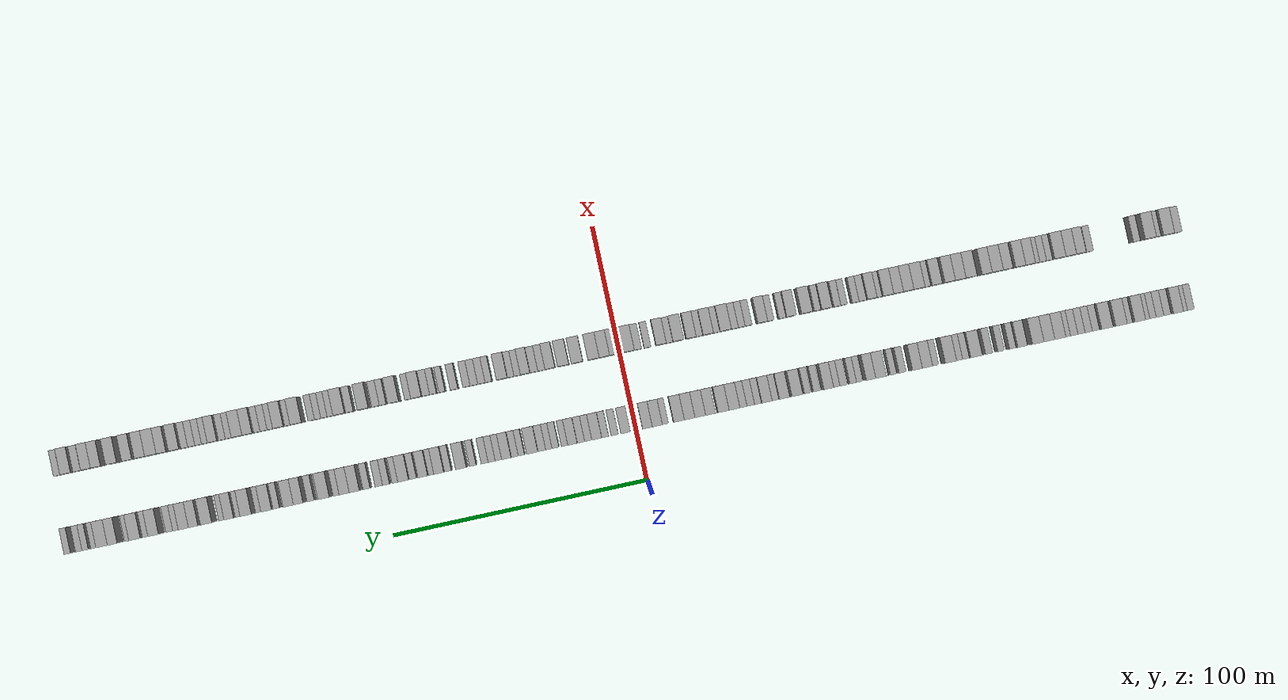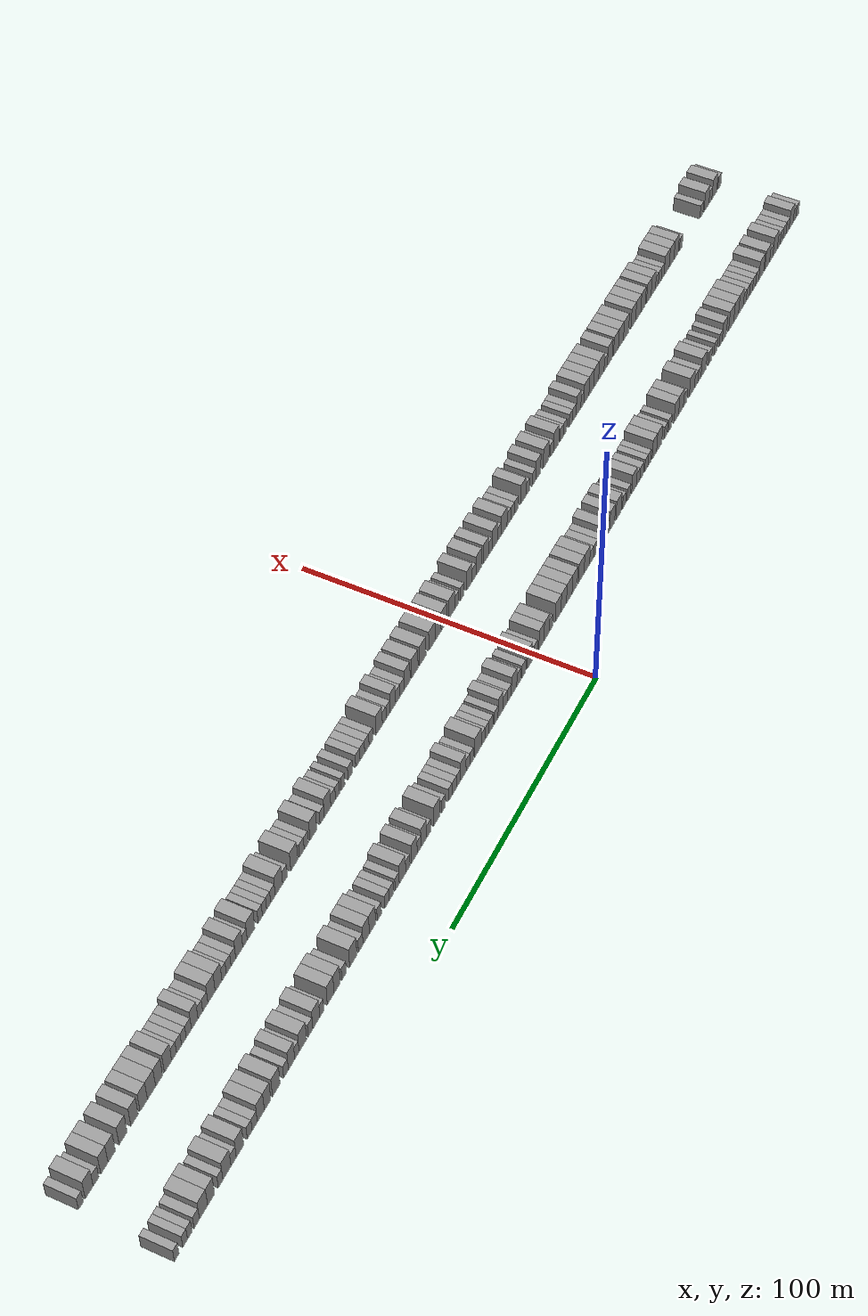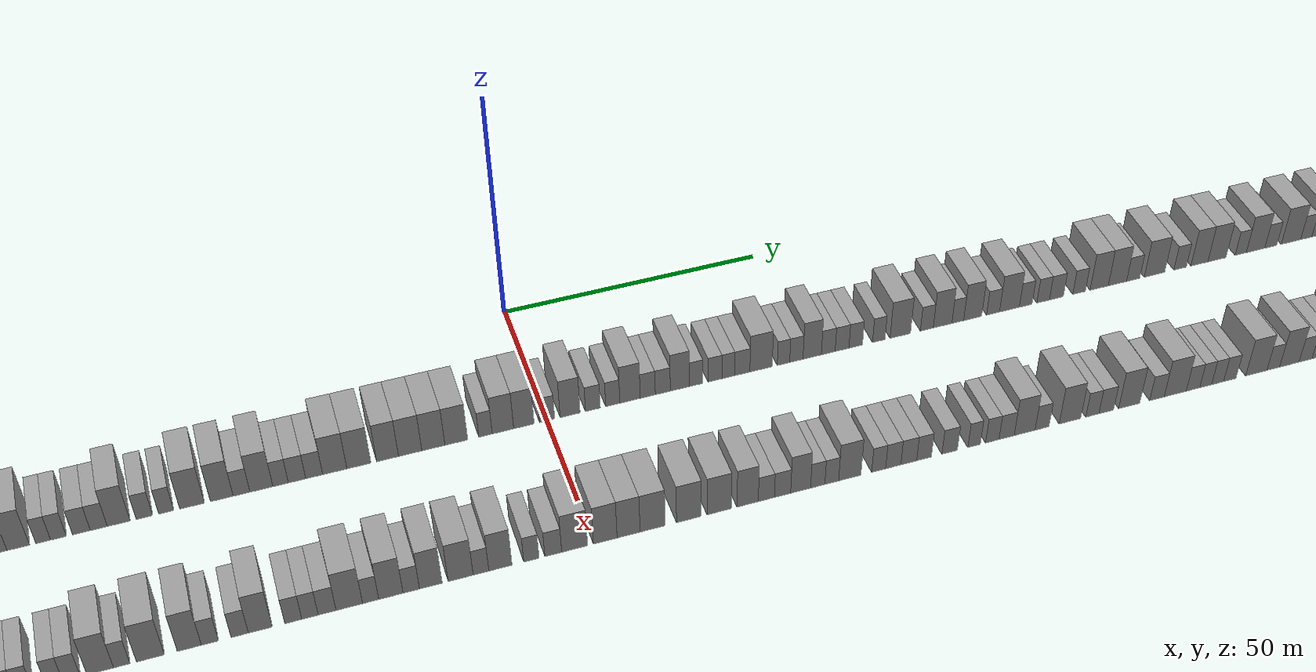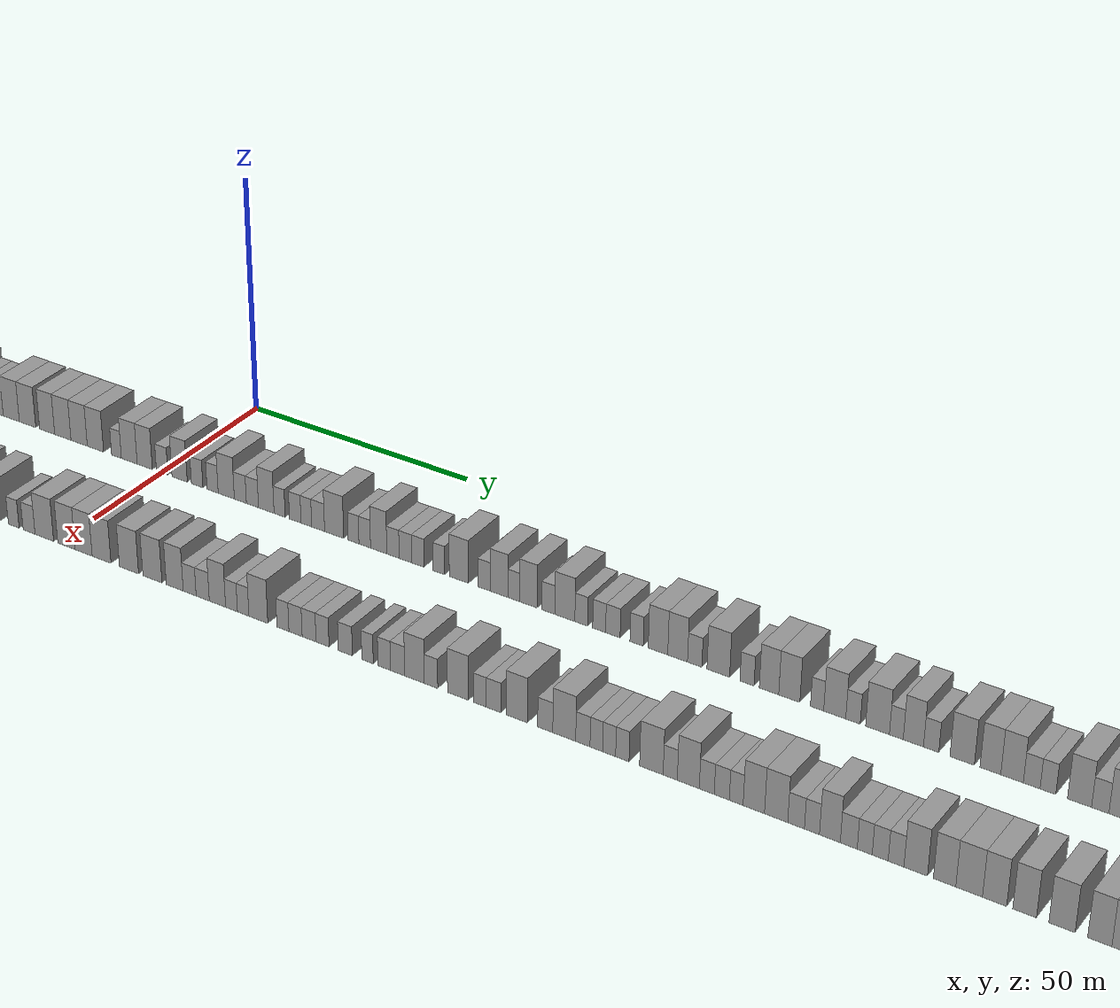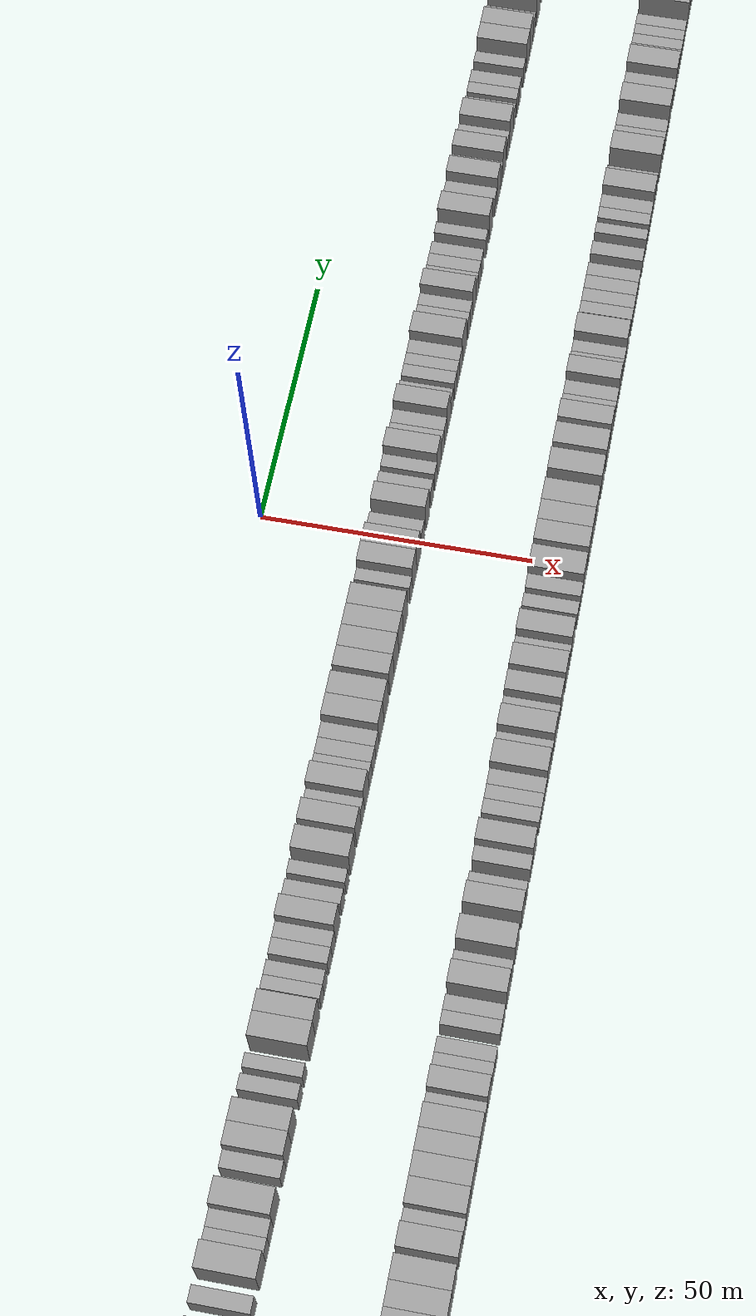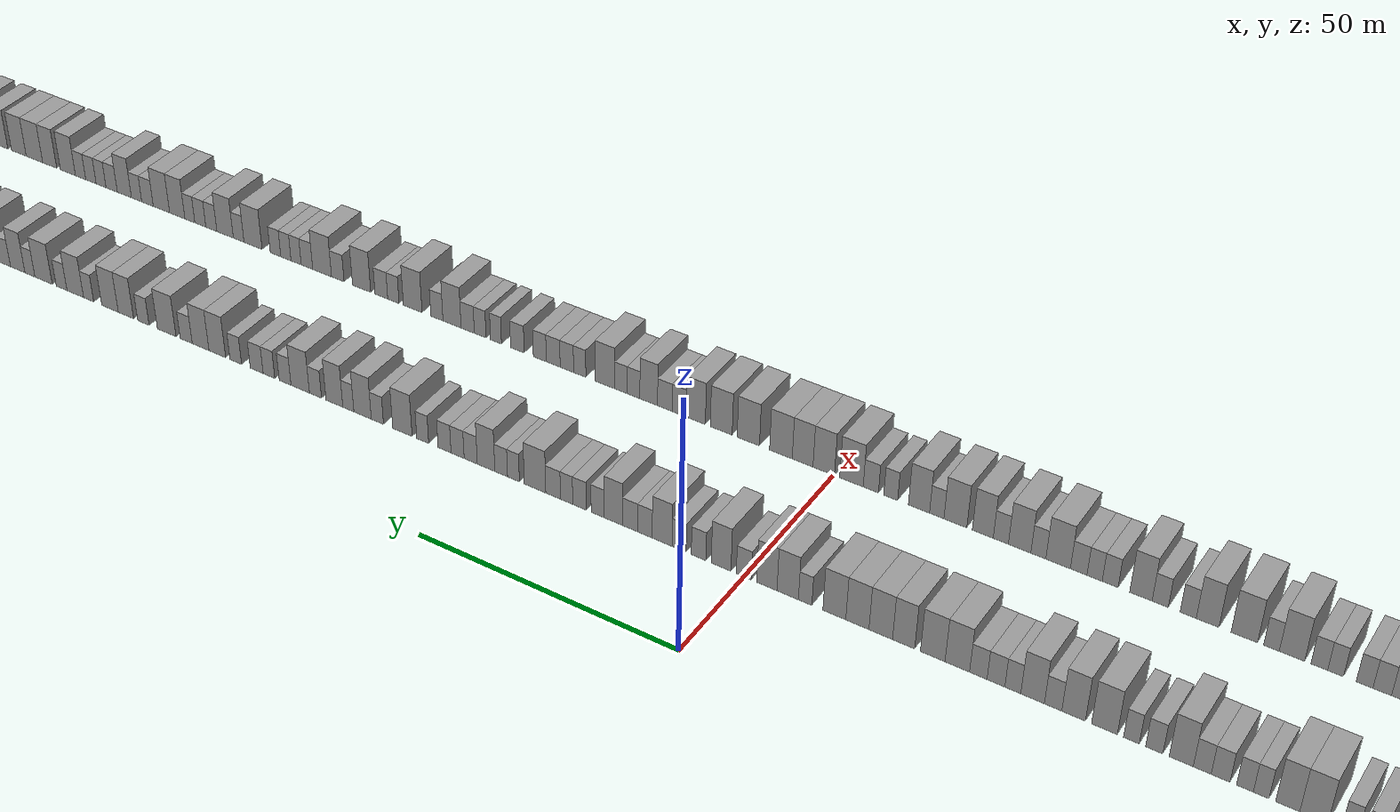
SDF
<sdf version="1.6">
 <world name="default">
  <scene>
   <sky><clouds><speed>12</speed></clouds></sky>
   <ambient>0.4 0.4 0.4 1</ambient>
   <background>0.7 0.7 0.7 1</background>
   <shadows>1</shadows>
  </scene>
  <gravity>0 0 -9.8066</gravity>
  <magnetic_field>6e-06 2.3e-05 -4.2e-05</magnetic_field>
  <physics default="0" name="default_physics" type="ode">
   <ode>
    <solver>
     <type>quick</type>
     <iters>10</iters>
     <sor>1.0</sor>
     <use_dynamic_moi_rescaling>0</use_dynamic_moi_rescaling>
    </solver>
    <constraints>
     <cfm>0</cfm>
     <erp>0.2</erp>
     <contact_max_correcting_vel>100</contact_max_correcting_vel>
     <contact_surface_layer>0.001</contact_surface_layer>
    </constraints>
   </ode>
   <max_step_size>0.004</max_step_size>
   <real_time_factor>1</real_time_factor>
   <real_time_update_rate>250</real_time_update_rate>
  </physics>
  <light name="sun" type="directional">
   <pose>0 0 10 0 0 0</pose>
   <diffuse>0.8 0.8 0.8 1</diffuse>
   <specular>0.2 0.2 0.2 1</specular>
   <attenuation>
    <range>1000</range>
    <constant>0.9</constant>
    <linear>0.01</linear>
    <quadratic>0.001</quadratic>
   </attenuation>
   <direction>-0.5 0.1 -0.9</direction>
  </light>
  <model name="building_1">
   <static>1</static>
   <pose>25.0000 -216.6692 0 0.000000 0.000000 0.000000</pose>
   <link name="link">
    <pose>0 0 3.00 0 0 0</pose>
    <collision name="collision"><geometry><box><size>10.0000 2.6616 6.0000</size></box></geometry></collision>
    <visual name="visual">
     <cast_shadows>0</cast_shadows>
     <geometry><box><size>10.0000 2.6616 6.0000</size></box></geometry>
     <material>
      <script>
       <uri>model://grey_wall/materials/scripts</uri>
       <uri>model://grey_wall/materials/textures</uri>
       <name>vrc/grey_wall</name>
      </script>
     </material>
    </visual>
   </link>
  </model>
  <model name="building_2">
   <static>1</static>
   <pose>25.0000 -214.0633 0 0.000000 0.000000 0.000000</pose>
   <link name="link">
    <pose>0 0 3.00 0 0 0</pose>
    <collision name="collision"><geometry><box><size>10.0000 2.5503 6.0000</size></box></geometry></collision>
    <visual name="visual">
     <cast_shadows>0</cast_shadows>
     <geometry><box><size>10.0000 2.5503 6.0000</size></box></geometry>
     <material>
      <script>
       <uri>model://grey_wall/materials/scripts</uri>
       <uri>model://grey_wall/materials/textures</uri>
       <name>vrc/grey_wall</name>
      </script>
     </material>
    </visual>
   </link>
  </model>
  <model name="building_3">
   <static>1</static>
   <pose>25.0000 -210.8497 0 0.000000 0.000000 0.000000</pose>
   <link name="link">
    <pose>0 0 4.50 0 0 0</pose>
    <collision name="collision"><geometry><box><size>10.0000 3.8767 9.0000</size></box></geometry></collision>
    <visual name="visual">
     <cast_shadows>0</cast_shadows>
     <geometry><box><size>10.0000 3.8767 9.0000</size></box></geometry>
     <material>
      <script>
       <uri>model://grey_wall/materials/scripts</uri>
       <uri>model://grey_wall/materials/textures</uri>
       <name>vrc/grey_wall</name>
      </script>
     </material>
    </visual>
   </link>
  </model>
  <model name="building_4">
   <static>1</static>
   <pose>25.0000 -207.5015 0 0.000000 0.000000 0.000000</pose>
   <link name="link">
    <pose>0 0 3.00 0 0 0</pose>
    <collision name="collision"><geometry><box><size>10.0000 2.8198 6.0000</size></box></geometry></collision>
    <visual name="visual">
     <cast_shadows>0</cast_shadows>
     <geometry><box><size>10.0000 2.8198 6.0000</size></box></geometry>
     <material>
      <script>
       <uri>model://grey_wall/materials/scripts</uri>
       <uri>model://grey_wall/materials/textures</uri>
       <name>vrc/grey_wall</name>
      </script>
     </material>
    </visual>
   </link>
  </model>
  <model name="building_5">
   <static>1</static>
   <pose>25.0000 -204.5973 0 0.000000 0.000000 0.000000</pose>
   <link name="link">
    <pose>0 0 3.00 0 0 0</pose>
    <collision name="collision"><geometry><box><size>10.0000 2.9886 6.0000</size></box></geometry></collision>
    <visual name="visual">
     <cast_shadows>0</cast_shadows>
     <geometry><box><size>10.0000 2.9886 6.0000</size></box></geometry>
     <material>
      <script>
       <uri>model://grey_wall/materials/scripts</uri>
       <uri>model://grey_wall/materials/textures</uri>
       <name>vrc/grey_wall</name>
      </script>
     </material>
    </visual>
   </link>
  </model>
  <model name="building_6">
   <static>1</static>
   <pose>25.0000 -201.8396 0 0.000000 0.000000 0.000000</pose>
   <link name="link">
    <pose>0 0 3.00 0 0 0</pose>
    <collision name="collision"><geometry><box><size>10.0000 2.5268 6.0000</size></box></geometry></collision>
    <visual name="visual">
     <cast_shadows>0</cast_shadows>
     <geometry><box><size>10.0000 2.5268 6.0000</size></box></geometry>
     <material>
      <script>
       <uri>model://grey_wall/materials/scripts</uri>
       <uri>model://grey_wall/materials/textures</uri>
       <name>vrc/grey_wall</name>
      </script>
     </material>
    </visual>
   </link>
  </model>
  <model name="building_7">
   <static>1</static>
   <pose>25.0000 -199.2995 0 0.000000 0.000000 0.000000</pose>
   <link name="link">
    <pose>0 0 3.00 0 0 0</pose>
    <collision name="collision"><geometry><box><size>10.0000 2.5535 6.0000</size></box></geometry></collision>
    <visual name="visual">
     <cast_shadows>0</cast_shadows>
     <geometry><box><size>10.0000 2.5535 6.0000</size></box></geometry>
     <material>
      <script>
       <uri>model://grey_wall/materials/scripts</uri>
       <uri>model://grey_wall/materials/textures</uri>
       <name>vrc/grey_wall</name>
      </script>
     </material>
    </visual>
   </link>
  </model>
  <model name="building_8">
   <static>1</static>
   <pose>25.0000 -195.9334 0 0.000000 0.000000 0.000000</pose>
   <link name="link">
    <pose>0 0 4.50 0 0 0</pose>
    <collision name="collision"><geometry><box><size>10.0000 4.1788 9.0000</size></box></geometry></collision>
    <visual name="visual">
     <cast_shadows>0</cast_shadows>
     <geometry><box><size>10.0000 4.1788 9.0000</size></box></geometry>
     <material>
      <script>
       <uri>model://grey_wall/materials/scripts</uri>
       <uri>model://grey_wall/materials/textures</uri>
       <name>vrc/grey_wall</name>
      </script>
     </material>
    </visual>
   </link>
  </model>
  <model name="building_9">
   <static>1</static>
   <pose>25.0000 -192.3451 0 0.000000 0.000000 0.000000</pose>
   <link name="link">
    <pose>0 0 3.00 0 0 0</pose>
    <collision name="collision"><geometry><box><size>10.0000 2.9979 6.0000</size></box></geometry></collision>
    <visual name="visual">
     <cast_shadows>0</cast_shadows>
     <geometry><box><size>10.0000 2.9979 6.0000</size></box></geometry>
     <material>
      <script>
       <uri>model://grey_wall/materials/scripts</uri>
       <uri>model://grey_wall/materials/textures</uri>
       <name>vrc/grey_wall</name>
      </script>
     </material>
    </visual>
   </link>
  </model>
  <model name="building_10">
   <static>1</static>
   <pose>25.0000 -188.6095 0 0.000000 0.000000 0.000000</pose>
   <link name="link">
    <pose>0 0 4.50 0 0 0</pose>
    <collision name="collision"><geometry><box><size>10.0000 4.4733 9.0000</size></box></geometry></collision>
    <visual name="visual">
     <cast_shadows>0</cast_shadows>
     <geometry><box><size>10.0000 4.4733 9.0000</size></box></geometry>
     <material>
      <script>
       <uri>model://grey_wall/materials/scripts</uri>
       <uri>model://grey_wall/materials/textures</uri>
       <name>vrc/grey_wall</name>
      </script>
     </material>
    </visual>
   </link>
  </model>
  <model name="building_11">
   <static>1</static>
   <pose>25.0000 -183.1339 0 0.000000 0.000000 0.000000</pose>
   <link name="link">
    <pose>0 0 4.50 0 0 0</pose>
    <collision name="collision"><geometry><box><size>10.0000 4.4779 9.0000</size></box></geometry></collision>
    <visual name="visual">
     <cast_shadows>0</cast_shadows>
     <geometry><box><size>10.0000 4.4779 9.0000</size></box></geometry>
     <material>
      <script>
       <uri>model://grey_wall/materials/scripts</uri>
       <uri>model://grey_wall/materials/textures</uri>
       <name>vrc/grey_wall</name>
      </script>
     </material>
    </visual>
   </link>
  </model>
  <model name="building_12">
   <static>1</static>
   <pose>25.0000 -179.4846 0 0.000000 0.000000 0.000000</pose>
   <link name="link">
    <pose>0 0 3.00 0 0 0</pose>
    <collision name="collision"><geometry><box><size>10.0000 2.8207 6.0000</size></box></geometry></collision>
    <visual name="visual">
     <cast_shadows>0</cast_shadows>
     <geometry><box><size>10.0000 2.8207 6.0000</size></box></geometry>
     <material>
      <script>
       <uri>model://grey_wall/materials/scripts</uri>
       <uri>model://grey_wall/materials/textures</uri>
       <name>vrc/grey_wall</name>
      </script>
     </material>
    </visual>
   </link>
  </model>
  <model name="building_13">
   <static>1</static>
   <pose>25.0000 -176.6649 0 0.000000 0.000000 0.000000</pose>
   <link name="link">
    <pose>0 0 3.00 0 0 0</pose>
    <collision name="collision"><geometry><box><size>10.0000 2.8188 6.0000</size></box></geometry></collision>
    <visual name="visual">
     <cast_shadows>0</cast_shadows>
     <geometry><box><size>10.0000 2.8188 6.0000</size></box></geometry>
     <material>
      <script>
       <uri>model://grey_wall/materials/scripts</uri>
       <uri>model://grey_wall/materials/textures</uri>
       <name>vrc/grey_wall</name>
      </script>
     </material>
    </visual>
   </link>
  </model>
  <model name="building_14">
   <static>1</static>
   <pose>25.0000 -173.8461 0 0.000000 0.000000 0.000000</pose>
   <link name="link">
    <pose>0 0 3.00 0 0 0</pose>
    <collision name="collision"><geometry><box><size>10.0000 2.8188 6.0000</size></box></geometry></collision>
    <visual name="visual">
     <cast_shadows>0</cast_shadows>
     <geometry><box><size>10.0000 2.8188 6.0000</size></box></geometry>
     <material>
      <script>
       <uri>model://grey_wall/materials/scripts</uri>
       <uri>model://grey_wall/materials/textures</uri>
       <name>vrc/grey_wall</name>
      </script>
     </material>
    </visual>
   </link>
  </model>
  <model name="building_15">
   <static>1</static>
   <pose>25.0000 -170.9920 0 0.000000 0.000000 0.000000</pose>
   <link name="link">
    <pose>0 0 3.00 0 0 0</pose>
    <collision name="collision"><geometry><box><size>10.0000 2.8892 6.0000</size></box></geometry></collision>
    <visual name="visual">
     <cast_shadows>0</cast_shadows>
     <geometry><box><size>10.0000 2.8892 6.0000</size></box></geometry>
     <material>
      <script>
       <uri>model://grey_wall/materials/scripts</uri>
       <uri>model://grey_wall/materials/textures</uri>
       <name>vrc/grey_wall</name>
      </script>
     </material>
    </visual>
   </link>
  </model>
  <model name="building_16">
   <static>1</static>
   <pose>25.0000 -168.2565 0 0.000000 0.000000 0.000000</pose>
   <link name="link">
    <pose>0 0 3.00 0 0 0</pose>
    <collision name="collision"><geometry><box><size>10.0000 2.5820 6.0000</size></box></geometry></collision>
    <visual name="visual">
     <cast_shadows>0</cast_shadows>
     <geometry><box><size>10.0000 2.5820 6.0000</size></box></geometry>
     <material>
      <script>
       <uri>model://grey_wall/materials/scripts</uri>
       <uri>model://grey_wall/materials/textures</uri>
       <name>vrc/grey_wall</name>
      </script>
     </material>
    </visual>
   </link>
  </model>
  <model name="building_17">
   <static>1</static>
   <pose>25.0000 -164.8124 0 0.000000 0.000000 0.000000</pose>
   <link name="link">
    <pose>0 0 4.50 0 0 0</pose>
    <collision name="collision"><geometry><box><size>10.0000 4.3063 9.0000</size></box></geometry></collision>
    <visual name="visual">
     <cast_shadows>0</cast_shadows>
     <geometry><box><size>10.0000 4.3063 9.0000</size></box></geometry>
     <material>
      <script>
       <uri>model://grey_wall/materials/scripts</uri>
       <uri>model://grey_wall/materials/textures</uri>
       <name>vrc/grey_wall</name>
      </script>
     </material>
    </visual>
   </link>
  </model>
  <model name="building_18">
   <static>1</static>
   <pose>25.0000 -160.5485 0 0.000000 0.000000 0.000000</pose>
   <link name="link">
    <pose>0 0 4.50 0 0 0</pose>
    <collision name="collision"><geometry><box><size>10.0000 4.2215 9.0000</size></box></geometry></collision>
    <visual name="visual">
     <cast_shadows>0</cast_shadows>
     <geometry><box><size>10.0000 4.2215 9.0000</size></box></geometry>
     <material>
      <script>
       <uri>model://grey_wall/materials/scripts</uri>
       <uri>model://grey_wall/materials/textures</uri>
       <name>vrc/grey_wall</name>
      </script>
     </material>
    </visual>
   </link>
  </model>
  <model name="building_19">
   <static>1</static>
   <pose>25.0000 -156.2051 0 0.000000 0.000000 0.000000</pose>
   <link name="link">
    <pose>0 0 4.50 0 0 0</pose>
    <collision name="collision"><geometry><box><size>10.0000 4.4653 9.0000</size></box></geometry></collision>
    <visual name="visual">
     <cast_shadows>0</cast_shadows>
     <geometry><box><size>10.0000 4.4653 9.0000</size></box></geometry>
     <material>
      <script>
       <uri>model://grey_wall/materials/scripts</uri>
       <uri>model://grey_wall/materials/textures</uri>
       <name>vrc/grey_wall</name>
      </script>
     </material>
    </visual>
   </link>
  </model>
  <model name="building_20">
   <static>1</static>
   <pose>25.0000 -150.1015 0 0.000000 0.000000 0.000000</pose>
   <link name="link">
    <pose>0 0 4.50 0 0 0</pose>
    <collision name="collision"><geometry><box><size>10.0000 3.7419 9.0000</size></box></geometry></collision>
    <visual name="visual">
     <cast_shadows>0</cast_shadows>
     <geometry><box><size>10.0000 3.7419 9.0000</size></box></geometry>
     <material>
      <script>
       <uri>model://grey_wall/materials/scripts</uri>
       <uri>model://grey_wall/materials/textures</uri>
       <name>vrc/grey_wall</name>
      </script>
     </material>
    </visual>
   </link>
  </model>
  <model name="building_21">
   <static>1</static>
   <pose>25.0000 -146.9632 0 0.000000 0.000000 0.000000</pose>
   <link name="link">
    <pose>0 0 3.00 0 0 0</pose>
    <collision name="collision"><geometry><box><size>10.0000 2.5347 6.0000</size></box></geometry></collision>
    <visual name="visual">
     <cast_shadows>0</cast_shadows>
     <geometry><box><size>10.0000 2.5347 6.0000</size></box></geometry>
     <material>
      <script>
       <uri>model://grey_wall/materials/scripts</uri>
       <uri>model://grey_wall/materials/textures</uri>
       <name>vrc/grey_wall</name>
      </script>
     </material>
    </visual>
   </link>
  </model>
  <model name="building_22">
   <static>1</static>
   <pose>25.0000 -142.4264 0 0.000000 0.000000 0.000000</pose>
   <link name="link">
    <pose>0 0 3.00 0 0 0</pose>
    <collision name="collision"><geometry><box><size>10.0000 2.5390 6.0000</size></box></geometry></collision>
    <visual name="visual">
     <cast_shadows>0</cast_shadows>
     <geometry><box><size>10.0000 2.5390 6.0000</size></box></geometry>
     <material>
      <script>
       <uri>model://grey_wall/materials/scripts</uri>
       <uri>model://grey_wall/materials/textures</uri>
       <name>vrc/grey_wall</name>
      </script>
     </material>
    </visual>
   </link>
  </model>
  <model name="building_23">
   <static>1</static>
   <pose>25.0000 -137.7569 0 0.000000 0.000000 0.000000</pose>
   <link name="link">
    <pose>0 0 3.00 0 0 0</pose>
    <collision name="collision"><geometry><box><size>10.0000 2.7999 6.0000</size></box></geometry></collision>
    <visual name="visual">
     <cast_shadows>0</cast_shadows>
     <geometry><box><size>10.0000 2.7999 6.0000</size></box></geometry>
     <material>
      <script>
       <uri>model://grey_wall/materials/scripts</uri>
       <uri>model://grey_wall/materials/textures</uri>
       <name>vrc/grey_wall</name>
      </script>
     </material>
    </visual>
   </link>
  </model>
  <model name="building_24">
   <static>1</static>
   <pose>25.0000 -132.1491 0 0.000000 0.000000 0.000000</pose>
   <link name="link">
    <pose>0 0 4.50 0 0 0</pose>
    <collision name="collision"><geometry><box><size>10.0000 4.4158 9.0000</size></box></geometry></collision>
    <visual name="visual">
     <cast_shadows>0</cast_shadows>
     <geometry><box><size>10.0000 4.4158 9.0000</size></box></geometry>
     <material>
      <script>
       <uri>model://grey_wall/materials/scripts</uri>
       <uri>model://grey_wall/materials/textures</uri>
       <name>vrc/grey_wall</name>
      </script>
     </material>
    </visual>
   </link>
  </model>
  <model name="building_25">
   <static>1</static>
   <pose>25.0000 -128.6467 0 0.000000 0.000000 0.000000</pose>
   <link name="link">
    <pose>0 0 3.00 0 0 0</pose>
    <collision name="collision"><geometry><box><size>10.0000 2.5891 6.0000</size></box></geometry></collision>
    <visual name="visual">
     <cast_shadows>0</cast_shadows>
     <geometry><box><size>10.0000 2.5891 6.0000</size></box></geometry>
     <material>
      <script>
       <uri>model://grey_wall/materials/scripts</uri>
       <uri>model://grey_wall/materials/textures</uri>
       <name>vrc/grey_wall</name>
      </script>
     </material>
    </visual>
   </link>
  </model>
  <model name="building_26">
   <static>1</static>
   <pose>25.0000 -125.8734 0 0.000000 0.000000 0.000000</pose>
   <link name="link">
    <pose>0 0 3.00 0 0 0</pose>
    <collision name="collision"><geometry><box><size>10.0000 2.9575 6.0000</size></box></geometry></collision>
    <visual name="visual">
     <cast_shadows>0</cast_shadows>
     <geometry><box><size>10.0000 2.9575 6.0000</size></box></geometry>
     <material>
      <script>
       <uri>model://grey_wall/materials/scripts</uri>
       <uri>model://grey_wall/materials/textures</uri>
       <name>vrc/grey_wall</name>
      </script>
     </material>
    </visual>
   </link>
  </model>
  <model name="building_27">
   <static>1</static>
   <pose>25.0000 -122.1930 0 0.000000 0.000000 0.000000</pose>
   <link name="link">
    <pose>0 0 4.50 0 0 0</pose>
    <collision name="collision"><geometry><box><size>10.0000 4.4033 9.0000</size></box></geometry></collision>
    <visual name="visual">
     <cast_shadows>0</cast_shadows>
     <geometry><box><size>10.0000 4.4033 9.0000</size></box></geometry>
     <material>
      <script>
       <uri>model://grey_wall/materials/scripts</uri>
       <uri>model://grey_wall/materials/textures</uri>
       <name>vrc/grey_wall</name>
      </script>
     </material>
    </visual>
   </link>
  </model>
  <model name="building_28">
   <static>1</static>
   <pose>25.0000 -116.5215 0 0.000000 0.000000 0.000000</pose>
   <link name="link">
    <pose>0 0 3.00 0 0 0</pose>
    <collision name="collision"><geometry><box><size>10.0000 2.9397 6.0000</size></box></geometry></collision>
    <visual name="visual">
     <cast_shadows>0</cast_shadows>
     <geometry><box><size>10.0000 2.9397 6.0000</size></box></geometry>
     <material>
      <script>
       <uri>model://grey_wall/materials/scripts</uri>
       <uri>model://grey_wall/materials/textures</uri>
       <name>vrc/grey_wall</name>
      </script>
     </material>
    </visual>
   </link>
  </model>
  <model name="building_29">
   <static>1</static>
   <pose>25.0000 -113.0702 0 0.000000 0.000000 0.000000</pose>
   <link name="link">
    <pose>0 0 4.50 0 0 0</pose>
    <collision name="collision"><geometry><box><size>10.0000 3.9629 9.0000</size></box></geometry></collision>
    <visual name="visual">
     <cast_shadows>0</cast_shadows>
     <geometry><box><size>10.0000 3.9629 9.0000</size></box></geometry>
     <material>
      <script>
       <uri>model://grey_wall/materials/scripts</uri>
       <uri>model://grey_wall/materials/textures</uri>
       <name>vrc/grey_wall</name>
      </script>
     </material>
    </visual>
   </link>
  </model>
  <model name="building_30">
   <static>1</static>
   <pose>25.0000 -109.1704 0 0.000000 0.000000 0.000000</pose>
   <link name="link">
    <pose>0 0 4.50 0 0 0</pose>
    <collision name="collision"><geometry><box><size>10.0000 3.8366 9.0000</size></box></geometry></collision>
    <visual name="visual">
     <cast_shadows>0</cast_shadows>
     <geometry><box><size>10.0000 3.8366 9.0000</size></box></geometry>
     <material>
      <script>
       <uri>model://grey_wall/materials/scripts</uri>
       <uri>model://grey_wall/materials/textures</uri>
       <name>vrc/grey_wall</name>
      </script>
     </material>
    </visual>
   </link>
  </model>
  <model name="building_31">
   <static>1</static>
   <pose>25.0000 -103.8944 0 0.000000 0.000000 0.000000</pose>
   <link name="link">
    <pose>0 0 3.00 0 0 0</pose>
    <collision name="collision"><geometry><box><size>10.0000 2.7154 6.0000</size></box></geometry></collision>
    <visual name="visual">
     <cast_shadows>0</cast_shadows>
     <geometry><box><size>10.0000 2.7154 6.0000</size></box></geometry>
     <material>
      <script>
       <uri>model://grey_wall/materials/scripts</uri>
       <uri>model://grey_wall/materials/textures</uri>
       <name>vrc/grey_wall</name>
      </script>
     </material>
    </visual>
   </link>
  </model>
  <model name="building_32">
   <static>1</static>
   <pose>25.0000 -100.3244 0 0.000000 0.000000 0.000000</pose>
   <link name="link">
    <pose>0 0 3.00 0 0 0</pose>
    <collision name="collision"><geometry><box><size>10.0000 2.4247 6.0000</size></box></geometry></collision>
    <visual name="visual">
     <cast_shadows>0</cast_shadows>
     <geometry><box><size>10.0000 2.4247 6.0000</size></box></geometry>
     <material>
      <script>
       <uri>model://grey_wall/materials/scripts</uri>
       <uri>model://grey_wall/materials/textures</uri>
       <name>vrc/grey_wall</name>
      </script>
     </material>
    </visual>
   </link>
  </model>
  <model name="building_33">
   <static>1</static>
   <pose>25.0000 -95.0097 0 0.000000 0.000000 0.000000</pose>
   <link name="link">
    <pose>0 0 4.50 0 0 0</pose>
    <collision name="collision"><geometry><box><size>10.0000 4.2046 9.0000</size></box></geometry></collision>
    <visual name="visual">
     <cast_shadows>0</cast_shadows>
     <geometry><box><size>10.0000 4.2046 9.0000</size></box></geometry>
     <material>
      <script>
       <uri>model://grey_wall/materials/scripts</uri>
       <uri>model://grey_wall/materials/textures</uri>
       <name>vrc/grey_wall</name>
      </script>
     </material>
    </visual>
   </link>
  </model>
  <model name="building_34">
   <static>1</static>
   <pose>25.0000 -91.0853 0 0.000000 0.000000 0.000000</pose>
   <link name="link">
    <pose>0 0 4.50 0 0 0</pose>
    <collision name="collision"><geometry><box><size>10.0000 3.6442 9.0000</size></box></geometry></collision>
    <visual name="visual">
     <cast_shadows>0</cast_shadows>
     <geometry><box><size>10.0000 3.6442 9.0000</size></box></geometry>
     <material>
      <script>
       <uri>model://grey_wall/materials/scripts</uri>
       <uri>model://grey_wall/materials/textures</uri>
       <name>vrc/grey_wall</name>
      </script>
     </material>
    </visual>
   </link>
  </model>
  <model name="building_35">
   <static>1</static>
   <pose>25.0000 -87.0597 0 0.000000 0.000000 0.000000</pose>
   <link name="link">
    <pose>0 0 3.00 0 0 0</pose>
    <collision name="collision"><geometry><box><size>10.0000 2.4070 6.0000</size></box></geometry></collision>
    <visual name="visual">
     <cast_shadows>0</cast_shadows>
     <geometry><box><size>10.0000 2.4070 6.0000</size></box></geometry>
     <material>
      <script>
       <uri>model://grey_wall/materials/scripts</uri>
       <uri>model://grey_wall/materials/textures</uri>
       <name>vrc/grey_wall</name>
      </script>
     </material>
    </visual>
   </link>
  </model>
  <model name="building_36">
   <static>1</static>
   <pose>25.0000 -84.5684 0 0.000000 0.000000 0.000000</pose>
   <link name="link">
    <pose>0 0 3.00 0 0 0</pose>
    <collision name="collision"><geometry><box><size>10.0000 2.5756 6.0000</size></box></geometry></collision>
    <visual name="visual">
     <cast_shadows>0</cast_shadows>
     <geometry><box><size>10.0000 2.5756 6.0000</size></box></geometry>
     <material>
      <script>
       <uri>model://grey_wall/materials/scripts</uri>
       <uri>model://grey_wall/materials/textures</uri>
       <name>vrc/grey_wall</name>
      </script>
     </material>
    </visual>
   </link>
  </model>
  <model name="building_37">
   <static>1</static>
   <pose>25.0000 -80.8199 0 0.000000 0.000000 0.000000</pose>
   <link name="link">
    <pose>0 0 3.00 0 0 0</pose>
    <collision name="collision"><geometry><box><size>10.0000 2.9214 6.0000</size></box></geometry></collision>
    <visual name="visual">
     <cast_shadows>0</cast_shadows>
     <geometry><box><size>10.0000 2.9214 6.0000</size></box></geometry>
     <material>
      <script>
       <uri>model://grey_wall/materials/scripts</uri>
       <uri>model://grey_wall/materials/textures</uri>
       <name>vrc/grey_wall</name>
      </script>
     </material>
    </visual>
   </link>
  </model>
  <model name="building_38">
   <static>1</static>
   <pose>25.0000 -77.9634 0 0.000000 0.000000 0.000000</pose>
   <link name="link">
    <pose>0 0 3.00 0 0 0</pose>
    <collision name="collision"><geometry><box><size>10.0000 2.7915 6.0000</size></box></geometry></collision>
    <visual name="visual">
     <cast_shadows>0</cast_shadows>
     <geometry><box><size>10.0000 2.7915 6.0000</size></box></geometry>
     <material>
      <script>
       <uri>model://grey_wall/materials/scripts</uri>
       <uri>model://grey_wall/materials/textures</uri>
       <name>vrc/grey_wall</name>
      </script>
     </material>
    </visual>
   </link>
  </model>
  <model name="building_39">
   <static>1</static>
   <pose>25.0000 -74.6773 0 0.000000 0.000000 0.000000</pose>
   <link name="link">
    <pose>0 0 4.50 0 0 0</pose>
    <collision name="collision"><geometry><box><size>10.0000 3.7808 9.0000</size></box></geometry></collision>
    <visual name="visual">
     <cast_shadows>0</cast_shadows>
     <geometry><box><size>10.0000 3.7808 9.0000</size></box></geometry>
     <material>
      <script>
       <uri>model://grey_wall/materials/scripts</uri>
       <uri>model://grey_wall/materials/textures</uri>
       <name>vrc/grey_wall</name>
      </script>
     </material>
    </visual>
   </link>
  </model>
  <model name="building_40">
   <static>1</static>
   <pose>25.0000 -70.4154 0 0.000000 0.000000 0.000000</pose>
   <link name="link">
    <pose>0 0 3.00 0 0 0</pose>
    <collision name="collision"><geometry><box><size>10.0000 2.7430 6.0000</size></box></geometry></collision>
    <visual name="visual">
     <cast_shadows>0</cast_shadows>
     <geometry><box><size>10.0000 2.7430 6.0000</size></box></geometry>
     <material>
      <script>
       <uri>model://grey_wall/materials/scripts</uri>
       <uri>model://grey_wall/materials/textures</uri>
       <name>vrc/grey_wall</name>
      </script>
     </material>
    </visual>
   </link>
  </model>
  <model name="building_41">
   <static>1</static>
   <pose>25.0000 -66.7813 0 0.000000 0.000000 0.000000</pose>
   <link name="link">
    <pose>0 0 3.00 0 0 0</pose>
    <collision name="collision"><geometry><box><size>10.0000 2.5254 6.0000</size></box></geometry></collision>
    <visual name="visual">
     <cast_shadows>0</cast_shadows>
     <geometry><box><size>10.0000 2.5254 6.0000</size></box></geometry>
     <material>
      <script>
       <uri>model://grey_wall/materials/scripts</uri>
       <uri>model://grey_wall/materials/textures</uri>
       <name>vrc/grey_wall</name>
      </script>
     </material>
    </visual>
   </link>
  </model>
  <model name="building_42">
   <static>1</static>
   <pose>25.0000 -62.4345 0 0.000000 0.000000 0.000000</pose>
   <link name="link">
    <pose>0 0 4.50 0 0 0</pose>
    <collision name="collision"><geometry><box><size>10.0000 4.1681 9.0000</size></box></geometry></collision>
    <visual name="visual">
     <cast_shadows>0</cast_shadows>
     <geometry><box><size>10.0000 4.1681 9.0000</size></box></geometry>
     <material>
      <script>
       <uri>model://grey_wall/materials/scripts</uri>
       <uri>model://grey_wall/materials/textures</uri>
       <name>vrc/grey_wall</name>
      </script>
     </material>
    </visual>
   </link>
  </model>
  <model name="building_43">
   <static>1</static>
   <pose>25.0000 -57.4151 0 0.000000 0.000000 0.000000</pose>
   <link name="link">
    <pose>0 0 4.50 0 0 0</pose>
    <collision name="collision"><geometry><box><size>10.0000 3.8708 9.0000</size></box></geometry></collision>
    <visual name="visual">
     <cast_shadows>0</cast_shadows>
     <geometry><box><size>10.0000 3.8708 9.0000</size></box></geometry>
     <material>
      <script>
       <uri>model://grey_wall/materials/scripts</uri>
       <uri>model://grey_wall/materials/textures</uri>
       <name>vrc/grey_wall</name>
      </script>
     </material>
    </visual>
   </link>
  </model>
  <model name="building_44">
   <static>1</static>
   <pose>25.0000 -54.0437 0 0.000000 0.000000 0.000000</pose>
   <link name="link">
    <pose>0 0 3.00 0 0 0</pose>
    <collision name="collision"><geometry><box><size>10.0000 2.8720 6.0000</size></box></geometry></collision>
    <visual name="visual">
     <cast_shadows>0</cast_shadows>
     <geometry><box><size>10.0000 2.8720 6.0000</size></box></geometry>
     <material>
      <script>
       <uri>model://grey_wall/materials/scripts</uri>
       <uri>model://grey_wall/materials/textures</uri>
       <name>vrc/grey_wall</name>
      </script>
     </material>
    </visual>
   </link>
  </model>
  <model name="building_45">
   <static>1</static>
   <pose>25.0000 -50.6438 0 0.000000 0.000000 0.000000</pose>
   <link name="link">
    <pose>0 0 4.50 0 0 0</pose>
    <collision name="collision"><geometry><box><size>10.0000 3.9276 9.0000</size></box></geometry></collision>
    <visual name="visual">
     <cast_shadows>0</cast_shadows>
     <geometry><box><size>10.0000 3.9276 9.0000</size></box></geometry>
     <material>
      <script>
       <uri>model://grey_wall/materials/scripts</uri>
       <uri>model://grey_wall/materials/textures</uri>
       <name>vrc/grey_wall</name>
      </script>
     </material>
    </visual>
   </link>
  </model>
  <model name="building_46">
   <static>1</static>
   <pose>25.0000 -47.3493 0 0.000000 0.000000 0.000000</pose>
   <link name="link">
    <pose>0 0 3.00 0 0 0</pose>
    <collision name="collision"><geometry><box><size>10.0000 2.6614 6.0000</size></box></geometry></collision>
    <visual name="visual">
     <cast_shadows>0</cast_shadows>
     <geometry><box><size>10.0000 2.6614 6.0000</size></box></geometry>
     <material>
      <script>
       <uri>model://grey_wall/materials/scripts</uri>
       <uri>model://grey_wall/materials/textures</uri>
       <name>vrc/grey_wall</name>
      </script>
     </material>
    </visual>
   </link>
  </model>
  <model name="building_47">
   <static>1</static>
   <pose>25.0000 -44.5205 0 0.000000 0.000000 0.000000</pose>
   <link name="link">
    <pose>0 0 3.00 0 0 0</pose>
    <collision name="collision"><geometry><box><size>10.0000 2.9962 6.0000</size></box></geometry></collision>
    <visual name="visual">
     <cast_shadows>0</cast_shadows>
     <geometry><box><size>10.0000 2.9962 6.0000</size></box></geometry>
     <material>
      <script>
       <uri>model://grey_wall/materials/scripts</uri>
       <uri>model://grey_wall/materials/textures</uri>
       <name>vrc/grey_wall</name>
      </script>
     </material>
    </visual>
   </link>
  </model>
  <model name="building_48">
   <static>1</static>
   <pose>25.0000 -41.5424 0 0.000000 0.000000 0.000000</pose>
   <link name="link">
    <pose>0 0 3.00 0 0 0</pose>
    <collision name="collision"><geometry><box><size>10.0000 2.9599 6.0000</size></box></geometry></collision>
    <visual name="visual">
     <cast_shadows>0</cast_shadows>
     <geometry><box><size>10.0000 2.9599 6.0000</size></box></geometry>
     <material>
      <script>
       <uri>model://grey_wall/materials/scripts</uri>
       <uri>model://grey_wall/materials/textures</uri>
       <name>vrc/grey_wall</name>
      </script>
     </material>
    </visual>
   </link>
  </model>
  <model name="building_49">
   <static>1</static>
   <pose>25.0000 -37.9625 0 0.000000 0.000000 0.000000</pose>
   <link name="link">
    <pose>0 0 4.50 0 0 0</pose>
    <collision name="collision"><geometry><box><size>10.0000 4.2000 9.0000</size></box></geometry></collision>
    <visual name="visual">
     <cast_shadows>0</cast_shadows>
     <geometry><box><size>10.0000 4.2000 9.0000</size></box></geometry>
     <material>
      <script>
       <uri>model://grey_wall/materials/scripts</uri>
       <uri>model://grey_wall/materials/textures</uri>
       <name>vrc/grey_wall</name>
      </script>
     </material>
    </visual>
   </link>
  </model>
  <model name="building_50">
   <static>1</static>
   <pose>25.0000 -33.7397 0 0.000000 0.000000 0.000000</pose>
   <link name="link">
    <pose>0 0 4.50 0 0 0</pose>
    <collision name="collision"><geometry><box><size>10.0000 4.2455 9.0000</size></box></geometry></collision>
    <visual name="visual">
     <cast_shadows>0</cast_shadows>
     <geometry><box><size>10.0000 4.2455 9.0000</size></box></geometry>
     <material>
      <script>
       <uri>model://grey_wall/materials/scripts</uri>
       <uri>model://grey_wall/materials/textures</uri>
       <name>vrc/grey_wall</name>
      </script>
     </material>
    </visual>
   </link>
  </model>
  <model name="building_51">
   <static>1</static>
   <pose>25.0000 -28.6835 0 0.000000 0.000000 0.000000</pose>
   <link name="link">
    <pose>0 0 4.50 0 0 0</pose>
    <collision name="collision"><geometry><box><size>10.0000 3.8669 9.0000</size></box></geometry></collision>
    <visual name="visual">
     <cast_shadows>0</cast_shadows>
     <geometry><box><size>10.0000 3.8669 9.0000</size></box></geometry>
     <material>
      <script>
       <uri>model://grey_wall/materials/scripts</uri>
       <uri>model://grey_wall/materials/textures</uri>
       <name>vrc/grey_wall</name>
      </script>
     </material>
    </visual>
   </link>
  </model>
  <model name="building_52">
   <static>1</static>
   <pose>25.0000 -24.6707 0 0.000000 0.000000 0.000000</pose>
   <link name="link">
    <pose>0 0 4.50 0 0 0</pose>
    <collision name="collision"><geometry><box><size>10.0000 4.1587 9.0000</size></box></geometry></collision>
    <visual name="visual">
     <cast_shadows>0</cast_shadows>
     <geometry><box><size>10.0000 4.1587 9.0000</size></box></geometry>
     <material>
      <script>
       <uri>model://grey_wall/materials/scripts</uri>
       <uri>model://grey_wall/materials/textures</uri>
       <name>vrc/grey_wall</name>
      </script>
     </material>
    </visual>
   </link>
  </model>
  <model name="building_53">
   <static>1</static>
   <pose>25.0000 -20.5302 0 0.000000 0.000000 0.000000</pose>
   <link name="link">
    <pose>0 0 4.50 0 0 0</pose>
    <collision name="collision"><geometry><box><size>10.0000 4.1223 9.0000</size></box></geometry></collision>
    <visual name="visual">
     <cast_shadows>0</cast_shadows>
     <geometry><box><size>10.0000 4.1223 9.0000</size></box></geometry>
     <material>
      <script>
       <uri>model://grey_wall/materials/scripts</uri>
       <uri>model://grey_wall/materials/textures</uri>
       <name>vrc/grey_wall</name>
      </script>
     </material>
    </visual>
   </link>
  </model>
  <model name="building_54">
   <static>1</static>
   <pose>25.0000 -16.4165 0 0.000000 0.000000 0.000000</pose>
   <link name="link">
    <pose>0 0 4.50 0 0 0</pose>
    <collision name="collision"><geometry><box><size>10.0000 4.1052 9.0000</size></box></geometry></collision>
    <visual name="visual">
     <cast_shadows>0</cast_shadows>
     <geometry><box><size>10.0000 4.1052 9.0000</size></box></geometry>
     <material>
      <script>
       <uri>model://grey_wall/materials/scripts</uri>
       <uri>model://grey_wall/materials/textures</uri>
       <name>vrc/grey_wall</name>
      </script>
     </material>
    </visual>
   </link>
  </model>
  <model name="building_55">
   <static>1</static>
   <pose>25.0000 -11.1443 0 0.000000 0.000000 0.000000</pose>
   <link name="link">
    <pose>0 0 3.00 0 0 0</pose>
    <collision name="collision"><geometry><box><size>10.0000 2.4392 6.0000</size></box></geometry></collision>
    <visual name="visual">
     <cast_shadows>0</cast_shadows>
     <geometry><box><size>10.0000 2.4392 6.0000</size></box></geometry>
     <material>
      <script>
       <uri>model://grey_wall/materials/scripts</uri>
       <uri>model://grey_wall/materials/textures</uri>
       <name>vrc/grey_wall</name>
      </script>
     </material>
    </visual>
   </link>
  </model>
  <model name="building_56">
   <static>1</static>
   <pose>25.0000 -7.9678 0 0.000000 0.000000 0.000000</pose>
   <link name="link">
    <pose>0 0 4.50 0 0 0</pose>
    <collision name="collision"><geometry><box><size>10.0000 3.9137 9.0000</size></box></geometry></collision>
    <visual name="visual">
     <cast_shadows>0</cast_shadows>
     <geometry><box><size>10.0000 3.9137 9.0000</size></box></geometry>
     <material>
      <script>
       <uri>model://grey_wall/materials/scripts</uri>
       <uri>model://grey_wall/materials/textures</uri>
       <name>vrc/grey_wall</name>
      </script>
     </material>
    </visual>
   </link>
  </model>
  <model name="building_57">
   <static>1</static>
   <pose>25.0000 -4.1392 0 0.000000 0.000000 0.000000</pose>
   <link name="link">
    <pose>0 0 4.50 0 0 0</pose>
    <collision name="collision"><geometry><box><size>10.0000 3.7436 9.0000</size></box></geometry></collision>
    <visual name="visual">
     <cast_shadows>0</cast_shadows>
     <geometry><box><size>10.0000 3.7436 9.0000</size></box></geometry>
     <material>
      <script>
       <uri>model://grey_wall/materials/scripts</uri>
       <uri>model://grey_wall/materials/textures</uri>
       <name>vrc/grey_wall</name>
      </script>
     </material>
    </visual>
   </link>
  </model>
  <model name="building_58">
   <static>1</static>
   <pose>25.0000 0.1297 0 0.000000 0.000000 0.000000</pose>
   <link name="link">
    <pose>0 0 3.00 0 0 0</pose>
    <collision name="collision"><geometry><box><size>10.0000 2.7941 6.0000</size></box></geometry></collision>
    <visual name="visual">
     <cast_shadows>0</cast_shadows>
     <geometry><box><size>10.0000 2.7941 6.0000</size></box></geometry>
     <material>
      <script>
       <uri>model://grey_wall/materials/scripts</uri>
       <uri>model://grey_wall/materials/textures</uri>
       <name>vrc/grey_wall</name>
      </script>
     </material>
    </visual>
   </link>
  </model>
  <model name="building_59">
   <static>1</static>
   <pose>25.0000 4.3772 0 0.000000 0.000000 0.000000</pose>
   <link name="link">
    <pose>0 0 4.50 0 0 0</pose>
    <collision name="collision"><geometry><box><size>10.0000 3.7009 9.0000</size></box></geometry></collision>
    <visual name="visual">
     <cast_shadows>0</cast_shadows>
     <geometry><box><size>10.0000 3.7009 9.0000</size></box></geometry>
     <material>
      <script>
       <uri>model://grey_wall/materials/scripts</uri>
       <uri>model://grey_wall/materials/textures</uri>
       <name>vrc/grey_wall</name>
      </script>
     </material>
    </visual>
   </link>
  </model>
  <model name="building_60">
   <static>1</static>
   <pose>25.0000 8.6152 0 0.000000 0.000000 0.000000</pose>
   <link name="link">
    <pose>0 0 3.00 0 0 0</pose>
    <collision name="collision"><geometry><box><size>10.0000 2.7752 6.0000</size></box></geometry></collision>
    <visual name="visual">
     <cast_shadows>0</cast_shadows>
     <geometry><box><size>10.0000 2.7752 6.0000</size></box></geometry>
     <material>
      <script>
       <uri>model://grey_wall/materials/scripts</uri>
       <uri>model://grey_wall/materials/textures</uri>
       <name>vrc/grey_wall</name>
      </script>
     </material>
    </visual>
   </link>
  </model>
  <model name="building_61">
   <static>1</static>
   <pose>25.0000 12.3280 0 0.000000 0.000000 0.000000</pose>
   <link name="link">
    <pose>0 0 3.00 0 0 0</pose>
    <collision name="collision"><geometry><box><size>10.0000 2.6505 6.0000</size></box></geometry></collision>
    <visual name="visual">
     <cast_shadows>0</cast_shadows>
     <geometry><box><size>10.0000 2.6505 6.0000</size></box></geometry>
     <material>
      <script>
       <uri>model://grey_wall/materials/scripts</uri>
       <uri>model://grey_wall/materials/textures</uri>
       <name>vrc/grey_wall</name>
      </script>
     </material>
    </visual>
   </link>
  </model>
  <model name="building_62">
   <static>1</static>
   <pose>25.0000 15.5733 0 0.000000 0.000000 0.000000</pose>
   <link name="link">
    <pose>0 0 4.50 0 0 0</pose>
    <collision name="collision"><geometry><box><size>10.0000 3.8400 9.0000</size></box></geometry></collision>
    <visual name="visual">
     <cast_shadows>0</cast_shadows>
     <geometry><box><size>10.0000 3.8400 9.0000</size></box></geometry>
     <material>
      <script>
       <uri>model://grey_wall/materials/scripts</uri>
       <uri>model://grey_wall/materials/textures</uri>
       <name>vrc/grey_wall</name>
      </script>
     </material>
    </visual>
   </link>
  </model>
  <model name="building_63">
   <static>1</static>
   <pose>25.0000 18.9208 0 0.000000 0.000000 0.000000</pose>
   <link name="link">
    <pose>0 0 3.00 0 0 0</pose>
    <collision name="collision"><geometry><box><size>10.0000 2.8550 6.0000</size></box></geometry></collision>
    <visual name="visual">
     <cast_shadows>0</cast_shadows>
     <geometry><box><size>10.0000 2.8550 6.0000</size></box></geometry>
     <material>
      <script>
       <uri>model://grey_wall/materials/scripts</uri>
       <uri>model://grey_wall/materials/textures</uri>
       <name>vrc/grey_wall</name>
      </script>
     </material>
    </visual>
   </link>
  </model>
  <model name="building_64">
   <static>1</static>
   <pose>25.0000 21.7757 0 0.000000 0.000000 0.000000</pose>
   <link name="link">
    <pose>0 0 3.00 0 0 0</pose>
    <collision name="collision"><geometry><box><size>10.0000 2.8547 6.0000</size></box></geometry></collision>
    <visual name="visual">
     <cast_shadows>0</cast_shadows>
     <geometry><box><size>10.0000 2.8547 6.0000</size></box></geometry>
     <material>
      <script>
       <uri>model://grey_wall/materials/scripts</uri>
       <uri>model://grey_wall/materials/textures</uri>
       <name>vrc/grey_wall</name>
      </script>
     </material>
    </visual>
   </link>
  </model>
  <model name="building_65">
   <static>1</static>
   <pose>25.0000 25.0209 0 0.000000 0.000000 0.000000</pose>
   <link name="link">
    <pose>0 0 4.50 0 0 0</pose>
    <collision name="collision"><geometry><box><size>10.0000 3.6357 9.0000</size></box></geometry></collision>
    <visual name="visual">
     <cast_shadows>0</cast_shadows>
     <geometry><box><size>10.0000 3.6357 9.0000</size></box></geometry>
     <material>
      <script>
       <uri>model://grey_wall/materials/scripts</uri>
       <uri>model://grey_wall/materials/textures</uri>
       <name>vrc/grey_wall</name>
      </script>
     </material>
    </visual>
   </link>
  </model>
  <model name="building_66">
   <static>1</static>
   <pose>25.0000 28.1320 0 0.000000 0.000000 0.000000</pose>
   <link name="link">
    <pose>0 0 3.00 0 0 0</pose>
    <collision name="collision"><geometry><box><size>10.0000 2.5865 6.0000</size></box></geometry></collision>
    <visual name="visual">
     <cast_shadows>0</cast_shadows>
     <geometry><box><size>10.0000 2.5865 6.0000</size></box></geometry>
     <material>
      <script>
       <uri>model://grey_wall/materials/scripts</uri>
       <uri>model://grey_wall/materials/textures</uri>
       <name>vrc/grey_wall</name>
      </script>
     </material>
    </visual>
   </link>
  </model>
  <model name="building_67">
   <static>1</static>
   <pose>25.0000 31.7616 0 0.000000 0.000000 0.000000</pose>
   <link name="link">
    <pose>0 0 3.00 0 0 0</pose>
    <collision name="collision"><geometry><box><size>10.0000 2.6728 6.0000</size></box></geometry></collision>
    <visual name="visual">
     <cast_shadows>0</cast_shadows>
     <geometry><box><size>10.0000 2.6728 6.0000</size></box></geometry>
     <material>
      <script>
       <uri>model://grey_wall/materials/scripts</uri>
       <uri>model://grey_wall/materials/textures</uri>
       <name>vrc/grey_wall</name>
      </script>
     </material>
    </visual>
   </link>
  </model>
  <model name="building_68">
   <static>1</static>
   <pose>25.0000 34.3246 0 0.000000 0.000000 0.000000</pose>
   <link name="link">
    <pose>0 0 3.00 0 0 0</pose>
    <collision name="collision"><geometry><box><size>10.0000 2.4531 6.0000</size></box></geometry></collision>
    <visual name="visual">
     <cast_shadows>0</cast_shadows>
     <geometry><box><size>10.0000 2.4531 6.0000</size></box></geometry>
     <material>
      <script>
       <uri>model://grey_wall/materials/scripts</uri>
       <uri>model://grey_wall/materials/textures</uri>
       <name>vrc/grey_wall</name>
      </script>
     </material>
    </visual>
   </link>
  </model>
  <model name="building_69">
   <static>1</static>
   <pose>25.0000 37.0264 0 0.000000 0.000000 0.000000</pose>
   <link name="link">
    <pose>0 0 3.00 0 0 0</pose>
    <collision name="collision"><geometry><box><size>10.0000 2.9506 6.0000</size></box></geometry></collision>
    <visual name="visual">
     <cast_shadows>0</cast_shadows>
     <geometry><box><size>10.0000 2.9506 6.0000</size></box></geometry>
     <material>
      <script>
       <uri>model://grey_wall/materials/scripts</uri>
       <uri>model://grey_wall/materials/textures</uri>
       <name>vrc/grey_wall</name>
      </script>
     </material>
    </visual>
   </link>
  </model>
  <model name="building_70">
   <static>1</static>
   <pose>25.0000 40.6774 0 0.000000 0.000000 0.000000</pose>
   <link name="link">
    <pose>0 0 4.50 0 0 0</pose>
    <collision name="collision"><geometry><box><size>10.0000 4.3513 9.0000</size></box></geometry></collision>
    <visual name="visual">
     <cast_shadows>0</cast_shadows>
     <geometry><box><size>10.0000 4.3513 9.0000</size></box></geometry>
     <material>
      <script>
       <uri>model://grey_wall/materials/scripts</uri>
       <uri>model://grey_wall/materials/textures</uri>
       <name>vrc/grey_wall</name>
      </script>
     </material>
    </visual>
   </link>
  </model>
  <model name="building_71">
   <static>1</static>
   <pose>25.0000 45.0658 0 0.000000 0.000000 0.000000</pose>
   <link name="link">
    <pose>0 0 3.00 0 0 0</pose>
    <collision name="collision"><geometry><box><size>10.0000 2.4256 6.0000</size></box></geometry></collision>
    <visual name="visual">
     <cast_shadows>0</cast_shadows>
     <geometry><box><size>10.0000 2.4256 6.0000</size></box></geometry>
     <material>
      <script>
       <uri>model://grey_wall/materials/scripts</uri>
       <uri>model://grey_wall/materials/textures</uri>
       <name>vrc/grey_wall</name>
      </script>
     </material>
    </visual>
   </link>
  </model>
  <model name="building_72">
   <static>1</static>
   <pose>25.0000 47.5848 0 0.000000 0.000000 0.000000</pose>
   <link name="link">
    <pose>0 0 3.00 0 0 0</pose>
    <collision name="collision"><geometry><box><size>10.0000 2.6124 6.0000</size></box></geometry></collision>
    <visual name="visual">
     <cast_shadows>0</cast_shadows>
     <geometry><box><size>10.0000 2.6124 6.0000</size></box></geometry>
     <material>
      <script>
       <uri>model://grey_wall/materials/scripts</uri>
       <uri>model://grey_wall/materials/textures</uri>
       <name>vrc/grey_wall</name>
      </script>
     </material>
    </visual>
   </link>
  </model>
  <model name="building_73">
   <static>1</static>
   <pose>25.0000 50.7102 0 0.000000 0.000000 0.000000</pose>
   <link name="link">
    <pose>0 0 4.50 0 0 0</pose>
    <collision name="collision"><geometry><box><size>10.0000 3.6385 9.0000</size></box></geometry></collision>
    <visual name="visual">
     <cast_shadows>0</cast_shadows>
     <geometry><box><size>10.0000 3.6385 9.0000</size></box></geometry>
     <material>
      <script>
       <uri>model://grey_wall/materials/scripts</uri>
       <uri>model://grey_wall/materials/textures</uri>
       <name>vrc/grey_wall</name>
      </script>
     </material>
    </visual>
   </link>
  </model>
  <model name="building_74">
   <static>1</static>
   <pose>25.0000 53.8976 0 0.000000 0.000000 0.000000</pose>
   <link name="link">
    <pose>0 0 3.00 0 0 0</pose>
    <collision name="collision"><geometry><box><size>10.0000 2.7363 6.0000</size></box></geometry></collision>
    <visual name="visual">
     <cast_shadows>0</cast_shadows>
     <geometry><box><size>10.0000 2.7363 6.0000</size></box></geometry>
     <material>
      <script>
       <uri>model://grey_wall/materials/scripts</uri>
       <uri>model://grey_wall/materials/textures</uri>
       <name>vrc/grey_wall</name>
      </script>
     </material>
    </visual>
   </link>
  </model>
  <model name="building_75">
   <static>1</static>
   <pose>25.0000 56.6421 0 0.000000 0.000000 0.000000</pose>
   <link name="link">
    <pose>0 0 3.00 0 0 0</pose>
    <collision name="collision"><geometry><box><size>10.0000 2.7527 6.0000</size></box></geometry></collision>
    <visual name="visual">
     <cast_shadows>0</cast_shadows>
     <geometry><box><size>10.0000 2.7527 6.0000</size></box></geometry>
     <material>
      <script>
       <uri>model://grey_wall/materials/scripts</uri>
       <uri>model://grey_wall/materials/textures</uri>
       <name>vrc/grey_wall</name>
      </script>
     </material>
    </visual>
   </link>
  </model>
  <model name="building_76">
   <static>1</static>
   <pose>25.0000 59.3777 0 0.000000 0.000000 0.000000</pose>
   <link name="link">
    <pose>0 0 3.00 0 0 0</pose>
    <collision name="collision"><geometry><box><size>10.0000 2.7184 6.0000</size></box></geometry></collision>
    <visual name="visual">
     <cast_shadows>0</cast_shadows>
     <geometry><box><size>10.0000 2.7184 6.0000</size></box></geometry>
     <material>
      <script>
       <uri>model://grey_wall/materials/scripts</uri>
       <uri>model://grey_wall/materials/textures</uri>
       <name>vrc/grey_wall</name>
      </script>
     </material>
    </visual>
   </link>
  </model>
  <model name="building_77">
   <static>1</static>
   <pose>25.0000 64.0012 0 0.000000 0.000000 0.000000</pose>
   <link name="link">
    <pose>0 0 3.00 0 0 0</pose>
    <collision name="collision"><geometry><box><size>10.0000 2.5286 6.0000</size></box></geometry></collision>
    <visual name="visual">
     <cast_shadows>0</cast_shadows>
     <geometry><box><size>10.0000 2.5286 6.0000</size></box></geometry>
     <material>
      <script>
       <uri>model://grey_wall/materials/scripts</uri>
       <uri>model://grey_wall/materials/textures</uri>
       <name>vrc/grey_wall</name>
      </script>
     </material>
    </visual>
   </link>
  </model>
  <model name="building_78">
   <static>1</static>
   <pose>25.0000 68.3409 0 0.000000 0.000000 0.000000</pose>
   <link name="link">
    <pose>0 0 4.50 0 0 0</pose>
    <collision name="collision"><geometry><box><size>10.0000 4.1508 9.0000</size></box></geometry></collision>
    <visual name="visual">
     <cast_shadows>0</cast_shadows>
     <geometry><box><size>10.0000 4.1508 9.0000</size></box></geometry>
     <material>
      <script>
       <uri>model://grey_wall/materials/scripts</uri>
       <uri>model://grey_wall/materials/textures</uri>
       <name>vrc/grey_wall</name>
      </script>
     </material>
    </visual>
   </link>
  </model>
  <model name="building_79">
   <static>1</static>
   <pose>25.0000 73.7358 0 0.000000 0.000000 0.000000</pose>
   <link name="link">
    <pose>0 0 3.00 0 0 0</pose>
    <collision name="collision"><geometry><box><size>10.0000 2.6390 6.0000</size></box></geometry></collision>
    <visual name="visual">
     <cast_shadows>0</cast_shadows>
     <geometry><box><size>10.0000 2.6390 6.0000</size></box></geometry>
     <material>
      <script>
       <uri>model://grey_wall/materials/scripts</uri>
       <uri>model://grey_wall/materials/textures</uri>
       <name>vrc/grey_wall</name>
      </script>
     </material>
    </visual>
   </link>
  </model>
  <model name="building_80">
   <static>1</static>
   <pose>25.0000 76.9606 0 0.000000 0.000000 0.000000</pose>
   <link name="link">
    <pose>0 0 4.50 0 0 0</pose>
    <collision name="collision"><geometry><box><size>10.0000 3.8106 9.0000</size></box></geometry></collision>
    <visual name="visual">
     <cast_shadows>0</cast_shadows>
     <geometry><box><size>10.0000 3.8106 9.0000</size></box></geometry>
     <material>
      <script>
       <uri>model://grey_wall/materials/scripts</uri>
       <uri>model://grey_wall/materials/textures</uri>
       <name>vrc/grey_wall</name>
      </script>
     </material>
    </visual>
   </link>
  </model>
  <model name="building_81">
   <static>1</static>
   <pose>25.0000 80.0798 0 0.000000 0.000000 0.000000</pose>
   <link name="link">
    <pose>0 0 3.00 0 0 0</pose>
    <collision name="collision"><geometry><box><size>10.0000 2.4279 6.0000</size></box></geometry></collision>
    <visual name="visual">
     <cast_shadows>0</cast_shadows>
     <geometry><box><size>10.0000 2.4279 6.0000</size></box></geometry>
     <material>
      <script>
       <uri>model://grey_wall/materials/scripts</uri>
       <uri>model://grey_wall/materials/textures</uri>
       <name>vrc/grey_wall</name>
      </script>
     </material>
    </visual>
   </link>
  </model>
  <model name="building_82">
   <static>1</static>
   <pose>25.0000 83.1506 0 0.000000 0.000000 0.000000</pose>
   <link name="link">
    <pose>0 0 4.50 0 0 0</pose>
    <collision name="collision"><geometry><box><size>10.0000 3.7137 9.0000</size></box></geometry></collision>
    <visual name="visual">
     <cast_shadows>0</cast_shadows>
     <geometry><box><size>10.0000 3.7137 9.0000</size></box></geometry>
     <material>
      <script>
       <uri>model://grey_wall/materials/scripts</uri>
       <uri>model://grey_wall/materials/textures</uri>
       <name>vrc/grey_wall</name>
      </script>
     </material>
    </visual>
   </link>
  </model>
  <model name="building_83">
   <static>1</static>
   <pose>25.0000 87.3602 0 0.000000 0.000000 0.000000</pose>
   <link name="link">
    <pose>0 0 3.00 0 0 0</pose>
    <collision name="collision"><geometry><box><size>10.0000 2.7054 6.0000</size></box></geometry></collision>
    <visual name="visual">
     <cast_shadows>0</cast_shadows>
     <geometry><box><size>10.0000 2.7054 6.0000</size></box></geometry>
     <material>
      <script>
       <uri>model://grey_wall/materials/scripts</uri>
       <uri>model://grey_wall/materials/textures</uri>
       <name>vrc/grey_wall</name>
      </script>
     </material>
    </visual>
   </link>
  </model>
  <model name="building_84">
   <static>1</static>
   <pose>25.0000 90.7812 0 0.000000 0.000000 0.000000</pose>
   <link name="link">
    <pose>0 0 4.50 0 0 0</pose>
    <collision name="collision"><geometry><box><size>10.0000 4.1368 9.0000</size></box></geometry></collision>
    <visual name="visual">
     <cast_shadows>0</cast_shadows>
     <geometry><box><size>10.0000 4.1368 9.0000</size></box></geometry>
     <material>
      <script>
       <uri>model://grey_wall/materials/scripts</uri>
       <uri>model://grey_wall/materials/textures</uri>
       <name>vrc/grey_wall</name>
      </script>
     </material>
    </visual>
   </link>
  </model>
  <model name="building_85">
   <static>1</static>
   <pose>25.0000 94.1807 0 0.000000 0.000000 0.000000</pose>
   <link name="link">
    <pose>0 0 3.00 0 0 0</pose>
    <collision name="collision"><geometry><box><size>10.0000 2.6621 6.0000</size></box></geometry></collision>
    <visual name="visual">
     <cast_shadows>0</cast_shadows>
     <geometry><box><size>10.0000 2.6621 6.0000</size></box></geometry>
     <material>
      <script>
       <uri>model://grey_wall/materials/scripts</uri>
       <uri>model://grey_wall/materials/textures</uri>
       <name>vrc/grey_wall</name>
      </script>
     </material>
    </visual>
   </link>
  </model>
  <model name="building_86">
   <static>1</static>
   <pose>25.0000 97.8368 0 0.000000 0.000000 0.000000</pose>
   <link name="link">
    <pose>0 0 3.00 0 0 0</pose>
    <collision name="collision"><geometry><box><size>10.0000 2.6501 6.0000</size></box></geometry></collision>
    <visual name="visual">
     <cast_shadows>0</cast_shadows>
     <geometry><box><size>10.0000 2.6501 6.0000</size></box></geometry>
     <material>
      <script>
       <uri>model://grey_wall/materials/scripts</uri>
       <uri>model://grey_wall/materials/textures</uri>
       <name>vrc/grey_wall</name>
      </script>
     </material>
    </visual>
   </link>
  </model>
  <model name="building_87">
   <static>1</static>
   <pose>25.0000 100.6346 0 0.000000 0.000000 0.000000</pose>
   <link name="link">
    <pose>0 0 3.00 0 0 0</pose>
    <collision name="collision"><geometry><box><size>10.0000 2.9455 6.0000</size></box></geometry></collision>
    <visual name="visual">
     <cast_shadows>0</cast_shadows>
     <geometry><box><size>10.0000 2.9455 6.0000</size></box></geometry>
     <material>
      <script>
       <uri>model://grey_wall/materials/scripts</uri>
       <uri>model://grey_wall/materials/textures</uri>
       <name>vrc/grey_wall</name>
      </script>
     </material>
    </visual>
   </link>
  </model>
  <model name="building_88">
   <static>1</static>
   <pose>25.0000 105.4472 0 0.000000 0.000000 0.000000</pose>
   <link name="link">
    <pose>0 0 3.00 0 0 0</pose>
    <collision name="collision"><geometry><box><size>10.0000 2.6798 6.0000</size></box></geometry></collision>
    <visual name="visual">
     <cast_shadows>0</cast_shadows>
     <geometry><box><size>10.0000 2.6798 6.0000</size></box></geometry>
     <material>
      <script>
       <uri>model://grey_wall/materials/scripts</uri>
       <uri>model://grey_wall/materials/textures</uri>
       <name>vrc/grey_wall</name>
      </script>
     </material>
    </visual>
   </link>
  </model>
  <model name="building_89">
   <static>1</static>
   <pose>25.0000 109.7364 0 0.000000 0.000000 0.000000</pose>
   <link name="link">
    <pose>0 0 4.50 0 0 0</pose>
    <collision name="collision"><geometry><box><size>10.0000 3.8987 9.0000</size></box></geometry></collision>
    <visual name="visual">
     <cast_shadows>0</cast_shadows>
     <geometry><box><size>10.0000 3.8987 9.0000</size></box></geometry>
     <material>
      <script>
       <uri>model://grey_wall/materials/scripts</uri>
       <uri>model://grey_wall/materials/textures</uri>
       <name>vrc/grey_wall</name>
      </script>
     </material>
    </visual>
   </link>
  </model>
  <model name="building_90">
   <static>1</static>
   <pose>25.0000 113.6498 0 0.000000 0.000000 0.000000</pose>
   <link name="link">
    <pose>0 0 4.50 0 0 0</pose>
    <collision name="collision"><geometry><box><size>10.0000 3.9279 9.0000</size></box></geometry></collision>
    <visual name="visual">
     <cast_shadows>0</cast_shadows>
     <geometry><box><size>10.0000 3.9279 9.0000</size></box></geometry>
     <material>
      <script>
       <uri>model://grey_wall/materials/scripts</uri>
       <uri>model://grey_wall/materials/textures</uri>
       <name>vrc/grey_wall</name>
      </script>
     </material>
    </visual>
   </link>
  </model>
  <model name="building_91">
   <static>1</static>
   <pose>25.0000 117.0299 0 0.000000 0.000000 0.000000</pose>
   <link name="link">
    <pose>0 0 3.00 0 0 0</pose>
    <collision name="collision"><geometry><box><size>10.0000 2.8324 6.0000</size></box></geometry></collision>
    <visual name="visual">
     <cast_shadows>0</cast_shadows>
     <geometry><box><size>10.0000 2.8324 6.0000</size></box></geometry>
     <material>
      <script>
       <uri>model://grey_wall/materials/scripts</uri>
       <uri>model://grey_wall/materials/textures</uri>
       <name>vrc/grey_wall</name>
      </script>
     </material>
    </visual>
   </link>
  </model>
  <model name="building_92">
   <static>1</static>
   <pose>25.0000 121.6636 0 0.000000 0.000000 0.000000</pose>
   <link name="link">
    <pose>0 0 4.50 0 0 0</pose>
    <collision name="collision"><geometry><box><size>10.0000 4.4349 9.0000</size></box></geometry></collision>
    <visual name="visual">
     <cast_shadows>0</cast_shadows>
     <geometry><box><size>10.0000 4.4349 9.0000</size></box></geometry>
     <material>
      <script>
       <uri>model://grey_wall/materials/scripts</uri>
       <uri>model://grey_wall/materials/textures</uri>
       <name>vrc/grey_wall</name>
      </script>
     </material>
    </visual>
   </link>
  </model>
  <model name="building_93">
   <static>1</static>
   <pose>25.0000 127.2473 0 0.000000 0.000000 0.000000</pose>
   <link name="link">
    <pose>0 0 3.00 0 0 0</pose>
    <collision name="collision"><geometry><box><size>10.0000 2.7326 6.0000</size></box></geometry></collision>
    <visual name="visual">
     <cast_shadows>0</cast_shadows>
     <geometry><box><size>10.0000 2.7326 6.0000</size></box></geometry>
     <material>
      <script>
       <uri>model://grey_wall/materials/scripts</uri>
       <uri>model://grey_wall/materials/textures</uri>
       <name>vrc/grey_wall</name>
      </script>
     </material>
    </visual>
   </link>
  </model>
  <model name="building_94">
   <static>1</static>
   <pose>25.0000 131.4762 0 0.000000 0.000000 0.000000</pose>
   <link name="link">
    <pose>0 0 4.50 0 0 0</pose>
    <collision name="collision"><geometry><box><size>10.0000 3.7252 9.0000</size></box></geometry></collision>
    <visual name="visual">
     <cast_shadows>0</cast_shadows>
     <geometry><box><size>10.0000 3.7252 9.0000</size></box></geometry>
     <material>
      <script>
       <uri>model://grey_wall/materials/scripts</uri>
       <uri>model://grey_wall/materials/textures</uri>
       <name>vrc/grey_wall</name>
      </script>
     </material>
    </visual>
   </link>
  </model>
  <model name="building_95">
   <static>1</static>
   <pose>25.0000 135.3518 0 0.000000 0.000000 0.000000</pose>
   <link name="link">
    <pose>0 0 4.50 0 0 0</pose>
    <collision name="collision"><geometry><box><size>10.0000 4.0258 9.0000</size></box></geometry></collision>
    <visual name="visual">
     <cast_shadows>0</cast_shadows>
     <geometry><box><size>10.0000 4.0258 9.0000</size></box></geometry>
     <material>
      <script>
       <uri>model://grey_wall/materials/scripts</uri>
       <uri>model://grey_wall/materials/textures</uri>
       <name>vrc/grey_wall</name>
      </script>
     </material>
    </visual>
   </link>
  </model>
  <model name="building_96">
   <static>1</static>
   <pose>25.0000 140.6121 0 0.000000 0.000000 0.000000</pose>
   <link name="link">
    <pose>0 0 3.00 0 0 0</pose>
    <collision name="collision"><geometry><box><size>10.0000 2.4949 6.0000</size></box></geometry></collision>
    <visual name="visual">
     <cast_shadows>0</cast_shadows>
     <geometry><box><size>10.0000 2.4949 6.0000</size></box></geometry>
     <material>
      <script>
       <uri>model://grey_wall/materials/scripts</uri>
       <uri>model://grey_wall/materials/textures</uri>
       <name>vrc/grey_wall</name>
      </script>
     </material>
    </visual>
   </link>
  </model>
  <model name="building_97">
   <static>1</static>
   <pose>25.0000 143.9246 0 0.000000 0.000000 0.000000</pose>
   <link name="link">
    <pose>0 0 4.50 0 0 0</pose>
    <collision name="collision"><geometry><box><size>10.0000 4.1300 9.0000</size></box></geometry></collision>
    <visual name="visual">
     <cast_shadows>0</cast_shadows>
     <geometry><box><size>10.0000 4.1300 9.0000</size></box></geometry>
     <material>
      <script>
       <uri>model://grey_wall/materials/scripts</uri>
       <uri>model://grey_wall/materials/textures</uri>
       <name>vrc/grey_wall</name>
      </script>
     </material>
    </visual>
   </link>
  </model>
  <model name="building_98">
   <static>1</static>
   <pose>25.0000 147.3326 0 0.000000 0.000000 0.000000</pose>
   <link name="link">
    <pose>0 0 3.00 0 0 0</pose>
    <collision name="collision"><geometry><box><size>10.0000 2.6861 6.0000</size></box></geometry></collision>
    <visual name="visual">
     <cast_shadows>0</cast_shadows>
     <geometry><box><size>10.0000 2.6861 6.0000</size></box></geometry>
     <material>
      <script>
       <uri>model://grey_wall/materials/scripts</uri>
       <uri>model://grey_wall/materials/textures</uri>
       <name>vrc/grey_wall</name>
      </script>
     </material>
    </visual>
   </link>
  </model>
  <model name="building_99">
   <static>1</static>
   <pose>25.0000 151.8672 0 0.000000 0.000000 0.000000</pose>
   <link name="link">
    <pose>0 0 4.50 0 0 0</pose>
    <collision name="collision"><geometry><box><size>10.0000 4.3831 9.0000</size></box></geometry></collision>
    <visual name="visual">
     <cast_shadows>0</cast_shadows>
     <geometry><box><size>10.0000 4.3831 9.0000</size></box></geometry>
     <material>
      <script>
       <uri>model://grey_wall/materials/scripts</uri>
       <uri>model://grey_wall/materials/textures</uri>
       <name>vrc/grey_wall</name>
      </script>
     </material>
    </visual>
   </link>
  </model>
  <model name="building_100">
   <static>1</static>
   <pose>25.0000 155.3198 0 0.000000 0.000000 0.000000</pose>
   <link name="link">
    <pose>0 0 3.00 0 0 0</pose>
    <collision name="collision"><geometry><box><size>10.0000 2.5220 6.0000</size></box></geometry></collision>
    <visual name="visual">
     <cast_shadows>0</cast_shadows>
     <geometry><box><size>10.0000 2.5220 6.0000</size></box></geometry>
     <material>
      <script>
       <uri>model://grey_wall/materials/scripts</uri>
       <uri>model://grey_wall/materials/textures</uri>
       <name>vrc/grey_wall</name>
      </script>
     </material>
    </visual>
   </link>
  </model>
  <model name="building_101">
   <static>1</static>
   <pose>25.0000 158.4260 0 0.000000 0.000000 0.000000</pose>
   <link name="link">
    <pose>0 0 4.50 0 0 0</pose>
    <collision name="collision"><geometry><box><size>10.0000 3.6906 9.0000</size></box></geometry></collision>
    <visual name="visual">
     <cast_shadows>0</cast_shadows>
     <geometry><box><size>10.0000 3.6906 9.0000</size></box></geometry>
     <material>
      <script>
       <uri>model://grey_wall/materials/scripts</uri>
       <uri>model://grey_wall/materials/textures</uri>
       <name>vrc/grey_wall</name>
      </script>
     </material>
    </visual>
   </link>
  </model>
  <model name="building_102">
   <static>1</static>
   <pose>25.0000 161.6524 0 0.000000 0.000000 0.000000</pose>
   <link name="link">
    <pose>0 0 3.00 0 0 0</pose>
    <collision name="collision"><geometry><box><size>10.0000 2.7621 6.0000</size></box></geometry></collision>
    <visual name="visual">
     <cast_shadows>0</cast_shadows>
     <geometry><box><size>10.0000 2.7621 6.0000</size></box></geometry>
     <material>
      <script>
       <uri>model://grey_wall/materials/scripts</uri>
       <uri>model://grey_wall/materials/textures</uri>
       <name>vrc/grey_wall</name>
      </script>
     </material>
    </visual>
   </link>
  </model>
  <model name="building_103">
   <static>1</static>
   <pose>25.0000 167.2128 0 0.000000 0.000000 0.000000</pose>
   <link name="link">
    <pose>0 0 4.50 0 0 0</pose>
    <collision name="collision"><geometry><box><size>10.0000 4.3587 9.0000</size></box></geometry></collision>
    <visual name="visual">
     <cast_shadows>0</cast_shadows>
     <geometry><box><size>10.0000 4.3587 9.0000</size></box></geometry>
     <material>
      <script>
       <uri>model://grey_wall/materials/scripts</uri>
       <uri>model://grey_wall/materials/textures</uri>
       <name>vrc/grey_wall</name>
      </script>
     </material>
    </visual>
   </link>
  </model>
  <model name="building_104">
   <static>1</static>
   <pose>25.0000 172.2282 0 0.000000 0.000000 0.000000</pose>
   <link name="link">
    <pose>0 0 4.50 0 0 0</pose>
    <collision name="collision"><geometry><box><size>10.0000 3.6721 9.0000</size></box></geometry></collision>
    <visual name="visual">
     <cast_shadows>0</cast_shadows>
     <geometry><box><size>10.0000 3.6721 9.0000</size></box></geometry>
     <material>
      <script>
       <uri>model://grey_wall/materials/scripts</uri>
       <uri>model://grey_wall/materials/textures</uri>
       <name>vrc/grey_wall</name>
      </script>
     </material>
    </visual>
   </link>
  </model>
  <model name="building_105">
   <static>1</static>
   <pose>25.0000 176.0439 0 0.000000 0.000000 0.000000</pose>
   <link name="link">
    <pose>0 0 4.50 0 0 0</pose>
    <collision name="collision"><geometry><box><size>10.0000 3.9592 9.0000</size></box></geometry></collision>
    <visual name="visual">
     <cast_shadows>0</cast_shadows>
     <geometry><box><size>10.0000 3.9592 9.0000</size></box></geometry>
     <material>
      <script>
       <uri>model://grey_wall/materials/scripts</uri>
       <uri>model://grey_wall/materials/textures</uri>
       <name>vrc/grey_wall</name>
      </script>
     </material>
    </visual>
   </link>
  </model>
  <model name="building_106">
   <static>1</static>
   <pose>25.0000 179.4803 0 0.000000 0.000000 0.000000</pose>
   <link name="link">
    <pose>0 0 3.00 0 0 0</pose>
    <collision name="collision"><geometry><box><size>10.0000 2.9138 6.0000</size></box></geometry></collision>
    <visual name="visual">
     <cast_shadows>0</cast_shadows>
     <geometry><box><size>10.0000 2.9138 6.0000</size></box></geometry>
     <material>
      <script>
       <uri>model://grey_wall/materials/scripts</uri>
       <uri>model://grey_wall/materials/textures</uri>
       <name>vrc/grey_wall</name>
      </script>
     </material>
    </visual>
   </link>
  </model>
  <model name="building_107">
   <static>1</static>
   <pose>25.0000 182.3056 0 0.000000 0.000000 0.000000</pose>
   <link name="link">
    <pose>0 0 3.00 0 0 0</pose>
    <collision name="collision"><geometry><box><size>10.0000 2.7368 6.0000</size></box></geometry></collision>
    <visual name="visual">
     <cast_shadows>0</cast_shadows>
     <geometry><box><size>10.0000 2.7368 6.0000</size></box></geometry>
     <material>
      <script>
       <uri>model://grey_wall/materials/scripts</uri>
       <uri>model://grey_wall/materials/textures</uri>
       <name>vrc/grey_wall</name>
      </script>
     </material>
    </visual>
   </link>
  </model>
  <model name="building_108">
   <static>1</static>
   <pose>25.0000 187.7296 0 0.000000 0.000000 0.000000</pose>
   <link name="link">
    <pose>0 0 4.50 0 0 0</pose>
    <collision name="collision"><geometry><box><size>10.0000 4.1111 9.0000</size></box></geometry></collision>
    <visual name="visual">
     <cast_shadows>0</cast_shadows>
     <geometry><box><size>10.0000 4.1111 9.0000</size></box></geometry>
     <material>
      <script>
       <uri>model://grey_wall/materials/scripts</uri>
       <uri>model://grey_wall/materials/textures</uri>
       <name>vrc/grey_wall</name>
      </script>
     </material>
    </visual>
   </link>
  </model>
  <model name="building_109">
   <static>1</static>
   <pose>25.0000 191.2585 0 0.000000 0.000000 0.000000</pose>
   <link name="link">
    <pose>0 0 3.00 0 0 0</pose>
    <collision name="collision"><geometry><box><size>10.0000 2.9467 6.0000</size></box></geometry></collision>
    <visual name="visual">
     <cast_shadows>0</cast_shadows>
     <geometry><box><size>10.0000 2.9467 6.0000</size></box></geometry>
     <material>
      <script>
       <uri>model://grey_wall/materials/scripts</uri>
       <uri>model://grey_wall/materials/textures</uri>
       <name>vrc/grey_wall</name>
      </script>
     </material>
    </visual>
   </link>
  </model>
  <model name="building_110">
   <static>1</static>
   <pose>25.0000 194.9466 0 0.000000 0.000000 0.000000</pose>
   <link name="link">
    <pose>0 0 4.50 0 0 0</pose>
    <collision name="collision"><geometry><box><size>10.0000 4.4295 9.0000</size></box></geometry></collision>
    <visual name="visual">
     <cast_shadows>0</cast_shadows>
     <geometry><box><size>10.0000 4.4295 9.0000</size></box></geometry>
     <material>
      <script>
       <uri>model://grey_wall/materials/scripts</uri>
       <uri>model://grey_wall/materials/textures</uri>
       <name>vrc/grey_wall</name>
      </script>
     </material>
    </visual>
   </link>
  </model>
  <model name="building_111">
   <static>1</static>
   <pose>25.0000 198.4334 0 0.000000 0.000000 0.000000</pose>
   <link name="link">
    <pose>0 0 3.00 0 0 0</pose>
    <collision name="collision"><geometry><box><size>10.0000 2.5440 6.0000</size></box></geometry></collision>
    <visual name="visual">
     <cast_shadows>0</cast_shadows>
     <geometry><box><size>10.0000 2.5440 6.0000</size></box></geometry>
     <material>
      <script>
       <uri>model://grey_wall/materials/scripts</uri>
       <uri>model://grey_wall/materials/textures</uri>
       <name>vrc/grey_wall</name>
      </script>
     </material>
    </visual>
   </link>
  </model>
  <model name="building_112">
   <static>1</static>
   <pose>25.0000 203.5893 0 0.000000 0.000000 0.000000</pose>
   <link name="link">
    <pose>0 0 4.50 0 0 0</pose>
    <collision name="collision"><geometry><box><size>10.0000 3.7680 9.0000</size></box></geometry></collision>
    <visual name="visual">
     <cast_shadows>0</cast_shadows>
     <geometry><box><size>10.0000 3.7680 9.0000</size></box></geometry>
     <material>
      <script>
       <uri>model://grey_wall/materials/scripts</uri>
       <uri>model://grey_wall/materials/textures</uri>
       <name>vrc/grey_wall</name>
      </script>
     </material>
    </visual>
   </link>
  </model>
  <model name="building_113">
   <static>1</static>
   <pose>25.0000 207.6919 0 0.000000 0.000000 0.000000</pose>
   <link name="link">
    <pose>0 0 4.50 0 0 0</pose>
    <collision name="collision"><geometry><box><size>10.0000 4.4371 9.0000</size></box></geometry></collision>
    <visual name="visual">
     <cast_shadows>0</cast_shadows>
     <geometry><box><size>10.0000 4.4371 9.0000</size></box></geometry>
     <material>
      <script>
       <uri>model://grey_wall/materials/scripts</uri>
       <uri>model://grey_wall/materials/textures</uri>
       <name>vrc/grey_wall</name>
      </script>
     </material>
    </visual>
   </link>
  </model>
  <model name="building_114">
   <static>1</static>
   <pose>25.0000 211.3695 0 0.000000 0.000000 0.000000</pose>
   <link name="link">
    <pose>0 0 3.00 0 0 0</pose>
    <collision name="collision"><geometry><box><size>10.0000 2.9181 6.0000</size></box></geometry></collision>
    <visual name="visual">
     <cast_shadows>0</cast_shadows>
     <geometry><box><size>10.0000 2.9181 6.0000</size></box></geometry>
     <material>
      <script>
       <uri>model://grey_wall/materials/scripts</uri>
       <uri>model://grey_wall/materials/textures</uri>
       <name>vrc/grey_wall</name>
      </script>
     </material>
    </visual>
   </link>
  </model>
  <model name="building_115">
   <static>1</static>
   <pose>25.0000 215.0455 0 0.000000 0.000000 0.000000</pose>
   <link name="link">
    <pose>0 0 3.00 0 0 0</pose>
    <collision name="collision"><geometry><box><size>10.0000 2.4340 6.0000</size></box></geometry></collision>
    <visual name="visual">
     <cast_shadows>0</cast_shadows>
     <geometry><box><size>10.0000 2.4340 6.0000</size></box></geometry>
     <material>
      <script>
       <uri>model://grey_wall/materials/scripts</uri>
       <uri>model://grey_wall/materials/textures</uri>
       <name>vrc/grey_wall</name>
      </script>
     </material>
    </visual>
   </link>
  </model>
  <model name="building_116">
   <static>1</static>
   <pose>25.0000 217.5165 0 0.000000 0.000000 0.000000</pose>
   <link name="link">
    <pose>0 0 3.00 0 0 0</pose>
    <collision name="collision"><geometry><box><size>10.0000 2.5080 6.0000</size></box></geometry></collision>
    <visual name="visual">
     <cast_shadows>0</cast_shadows>
     <geometry><box><size>10.0000 2.5080 6.0000</size></box></geometry>
     <material>
      <script>
       <uri>model://grey_wall/materials/scripts</uri>
       <uri>model://grey_wall/materials/textures</uri>
       <name>vrc/grey_wall</name>
      </script>
     </material>
    </visual>
   </link>
  </model>
  <model name="building_117">
   <static>1</static>
   <pose>25.0000 222.0105 0 0.000000 0.000000 0.000000</pose>
   <link name="link">
    <pose>0 0 3.00 0 0 0</pose>
    <collision name="collision"><geometry><box><size>10.0000 2.4799 6.0000</size></box></geometry></collision>
    <visual name="visual">
     <cast_shadows>0</cast_shadows>
     <geometry><box><size>10.0000 2.4799 6.0000</size></box></geometry>
     <material>
      <script>
       <uri>model://grey_wall/materials/scripts</uri>
       <uri>model://grey_wall/materials/textures</uri>
       <name>vrc/grey_wall</name>
      </script>
     </material>
    </visual>
   </link>
  </model>
  <model name="building_118">
   <static>1</static>
   <pose>55.0000 -218.5407 0 0.000000 0.000000 0.000000</pose>
   <link name="link">
    <pose>0 0 3.00 0 0 0</pose>
    <collision name="collision"><geometry><box><size>10.0000 2.9187 6.0000</size></box></geometry></collision>
    <visual name="visual">
     <cast_shadows>0</cast_shadows>
     <geometry><box><size>10.0000 2.9187 6.0000</size></box></geometry>
     <material>
      <script>
       <uri>model://grey_wall/materials/scripts</uri>
       <uri>model://grey_wall/materials/textures</uri>
       <name>vrc/grey_wall</name>
      </script>
     </material>
    </visual>
   </link>
  </model>
  <model name="building_119">
   <static>1</static>
   <pose>55.0000 -213.8973 0 0.000000 0.000000 0.000000</pose>
   <link name="link">
    <pose>0 0 4.50 0 0 0</pose>
    <collision name="collision"><geometry><box><size>10.0000 4.3681 9.0000</size></box></geometry></collision>
    <visual name="visual">
     <cast_shadows>0</cast_shadows>
     <geometry><box><size>10.0000 4.3681 9.0000</size></box></geometry>
     <material>
      <script>
       <uri>model://grey_wall/materials/scripts</uri>
       <uri>model://grey_wall/materials/textures</uri>
       <name>vrc/grey_wall</name>
      </script>
     </material>
    </visual>
   </link>
  </model>
  <model name="building_120">
   <static>1</static>
   <pose>55.0000 -210.3514 0 0.000000 0.000000 0.000000</pose>
   <link name="link">
    <pose>0 0 3.00 0 0 0</pose>
    <collision name="collision"><geometry><box><size>10.0000 2.7237 6.0000</size></box></geometry></collision>
    <visual name="visual">
     <cast_shadows>0</cast_shadows>
     <geometry><box><size>10.0000 2.7237 6.0000</size></box></geometry>
     <material>
      <script>
       <uri>model://grey_wall/materials/scripts</uri>
       <uri>model://grey_wall/materials/textures</uri>
       <name>vrc/grey_wall</name>
      </script>
     </material>
    </visual>
   </link>
  </model>
  <model name="building_121">
   <static>1</static>
   <pose>55.0000 -206.8050 0 0.000000 0.000000 0.000000</pose>
   <link name="link">
    <pose>0 0 4.50 0 0 0</pose>
    <collision name="collision"><geometry><box><size>10.0000 4.3690 9.0000</size></box></geometry></collision>
    <visual name="visual">
     <cast_shadows>0</cast_shadows>
     <geometry><box><size>10.0000 4.3690 9.0000</size></box></geometry>
     <material>
      <script>
       <uri>model://grey_wall/materials/scripts</uri>
       <uri>model://grey_wall/materials/textures</uri>
       <name>vrc/grey_wall</name>
      </script>
     </material>
    </visual>
   </link>
  </model>
  <model name="building_122">
   <static>1</static>
   <pose>55.0000 -202.2596 0 0.000000 0.000000 0.000000</pose>
   <link name="link">
    <pose>0 0 3.00 0 0 0</pose>
    <collision name="collision"><geometry><box><size>10.0000 2.7219 6.0000</size></box></geometry></collision>
    <visual name="visual">
     <cast_shadows>0</cast_shadows>
     <geometry><box><size>10.0000 2.7219 6.0000</size></box></geometry>
     <material>
      <script>
       <uri>model://grey_wall/materials/scripts</uri>
       <uri>model://grey_wall/materials/textures</uri>
       <name>vrc/grey_wall</name>
      </script>
     </material>
    </visual>
   </link>
  </model>
  <model name="building_123">
   <static>1</static>
   <pose>55.0000 -183.9188 0 0.000000 0.000000 0.000000</pose>
   <link name="link">
    <pose>0 0 3.00 0 0 0</pose>
    <collision name="collision"><geometry><box><size>10.0000 2.6532 6.0000</size></box></geometry></collision>
    <visual name="visual">
     <cast_shadows>0</cast_shadows>
     <geometry><box><size>10.0000 2.6532 6.0000</size></box></geometry>
     <material>
      <script>
       <uri>model://grey_wall/materials/scripts</uri>
       <uri>model://grey_wall/materials/textures</uri>
       <name>vrc/grey_wall</name>
      </script>
     </material>
    </visual>
   </link>
  </model>
  <model name="building_124">
   <static>1</static>
   <pose>55.0000 -179.7242 0 0.000000 0.000000 0.000000</pose>
   <link name="link">
    <pose>0 0 4.50 0 0 0</pose>
    <collision name="collision"><geometry><box><size>10.0000 3.7359 9.0000</size></box></geometry></collision>
    <visual name="visual">
     <cast_shadows>0</cast_shadows>
     <geometry><box><size>10.0000 3.7359 9.0000</size></box></geometry>
     <material>
      <script>
       <uri>model://grey_wall/materials/scripts</uri>
       <uri>model://grey_wall/materials/textures</uri>
       <name>vrc/grey_wall</name>
      </script>
     </material>
    </visual>
   </link>
  </model>
  <model name="building_125">
   <static>1</static>
   <pose>55.0000 -175.7832 0 0.000000 0.000000 0.000000</pose>
   <link name="link">
    <pose>0 0 4.50 0 0 0</pose>
    <collision name="collision"><geometry><box><size>10.0000 4.1460 9.0000</size></box></geometry></collision>
    <visual name="visual">
     <cast_shadows>0</cast_shadows>
     <geometry><box><size>10.0000 4.1460 9.0000</size></box></geometry>
     <material>
      <script>
       <uri>model://grey_wall/materials/scripts</uri>
       <uri>model://grey_wall/materials/textures</uri>
       <name>vrc/grey_wall</name>
      </script>
     </material>
    </visual>
   </link>
  </model>
  <model name="building_126">
   <static>1</static>
   <pose>55.0000 -171.4972 0 0.000000 0.000000 0.000000</pose>
   <link name="link">
    <pose>0 0 4.50 0 0 0</pose>
    <collision name="collision"><geometry><box><size>10.0000 4.4260 9.0000</size></box></geometry></collision>
    <visual name="visual">
     <cast_shadows>0</cast_shadows>
     <geometry><box><size>10.0000 4.4260 9.0000</size></box></geometry>
     <material>
      <script>
       <uri>model://grey_wall/materials/scripts</uri>
       <uri>model://grey_wall/materials/textures</uri>
       <name>vrc/grey_wall</name>
      </script>
     </material>
    </visual>
   </link>
  </model>
  <model name="building_127">
   <static>1</static>
   <pose>55.0000 -168.0741 0 0.000000 0.000000 0.000000</pose>
   <link name="link">
    <pose>0 0 3.00 0 0 0</pose>
    <collision name="collision"><geometry><box><size>10.0000 2.4201 6.0000</size></box></geometry></collision>
    <visual name="visual">
     <cast_shadows>0</cast_shadows>
     <geometry><box><size>10.0000 2.4201 6.0000</size></box></geometry>
     <material>
      <script>
       <uri>model://grey_wall/materials/scripts</uri>
       <uri>model://grey_wall/materials/textures</uri>
       <name>vrc/grey_wall</name>
      </script>
     </material>
    </visual>
   </link>
  </model>
  <model name="building_128">
   <static>1</static>
   <pose>55.0000 -165.5595 0 0.000000 0.000000 0.000000</pose>
   <link name="link">
    <pose>0 0 3.00 0 0 0</pose>
    <collision name="collision"><geometry><box><size>10.0000 2.6090 6.0000</size></box></geometry></collision>
    <visual name="visual">
     <cast_shadows>0</cast_shadows>
     <geometry><box><size>10.0000 2.6090 6.0000</size></box></geometry>
     <material>
      <script>
       <uri>model://grey_wall/materials/scripts</uri>
       <uri>model://grey_wall/materials/textures</uri>
       <name>vrc/grey_wall</name>
      </script>
     </material>
    </visual>
   </link>
  </model>
  <model name="building_129">
   <static>1</static>
   <pose>55.0000 -163.0246 0 0.000000 0.000000 0.000000</pose>
   <link name="link">
    <pose>0 0 3.00 0 0 0</pose>
    <collision name="collision"><geometry><box><size>10.0000 2.4610 6.0000</size></box></geometry></collision>
    <visual name="visual">
     <cast_shadows>0</cast_shadows>
     <geometry><box><size>10.0000 2.4610 6.0000</size></box></geometry>
     <material>
      <script>
       <uri>model://grey_wall/materials/scripts</uri>
       <uri>model://grey_wall/materials/textures</uri>
       <name>vrc/grey_wall</name>
      </script>
     </material>
    </visual>
   </link>
  </model>
  <model name="building_130">
   <static>1</static>
   <pose>55.0000 -159.9180 0 0.000000 0.000000 0.000000</pose>
   <link name="link">
    <pose>0 0 4.50 0 0 0</pose>
    <collision name="collision"><geometry><box><size>10.0000 3.7521 9.0000</size></box></geometry></collision>
    <visual name="visual">
     <cast_shadows>0</cast_shadows>
     <geometry><box><size>10.0000 3.7521 9.0000</size></box></geometry>
     <material>
      <script>
       <uri>model://grey_wall/materials/scripts</uri>
       <uri>model://grey_wall/materials/textures</uri>
       <name>vrc/grey_wall</name>
      </script>
     </material>
    </visual>
   </link>
  </model>
  <model name="building_131">
   <static>1</static>
   <pose>55.0000 -156.0631 0 0.000000 0.000000 0.000000</pose>
   <link name="link">
    <pose>0 0 4.50 0 0 0</pose>
    <collision name="collision"><geometry><box><size>10.0000 3.9577 9.0000</size></box></geometry></collision>
    <visual name="visual">
     <cast_shadows>0</cast_shadows>
     <geometry><box><size>10.0000 3.9577 9.0000</size></box></geometry>
     <material>
      <script>
       <uri>model://grey_wall/materials/scripts</uri>
       <uri>model://grey_wall/materials/textures</uri>
       <name>vrc/grey_wall</name>
      </script>
     </material>
    </visual>
   </link>
  </model>
  <model name="building_132">
   <static>1</static>
   <pose>55.0000 -151.1967 0 0.000000 0.000000 0.000000</pose>
   <link name="link">
    <pose>0 0 4.50 0 0 0</pose>
    <collision name="collision"><geometry><box><size>10.0000 3.7752 9.0000</size></box></geometry></collision>
    <visual name="visual">
     <cast_shadows>0</cast_shadows>
     <geometry><box><size>10.0000 3.7752 9.0000</size></box></geometry>
     <material>
      <script>
       <uri>model://grey_wall/materials/scripts</uri>
       <uri>model://grey_wall/materials/textures</uri>
       <name>vrc/grey_wall</name>
      </script>
     </material>
    </visual>
   </link>
  </model>
  <model name="building_133">
   <static>1</static>
   <pose>55.0000 -147.1388 0 0.000000 0.000000 0.000000</pose>
   <link name="link">
    <pose>0 0 4.50 0 0 0</pose>
    <collision name="collision"><geometry><box><size>10.0000 4.3406 9.0000</size></box></geometry></collision>
    <visual name="visual">
     <cast_shadows>0</cast_shadows>
     <geometry><box><size>10.0000 4.3406 9.0000</size></box></geometry>
     <material>
      <script>
       <uri>model://grey_wall/materials/scripts</uri>
       <uri>model://grey_wall/materials/textures</uri>
       <name>vrc/grey_wall</name>
      </script>
     </material>
    </visual>
   </link>
  </model>
  <model name="building_134">
   <static>1</static>
   <pose>55.0000 -143.0027 0 0.000000 0.000000 0.000000</pose>
   <link name="link">
    <pose>0 0 4.50 0 0 0</pose>
    <collision name="collision"><geometry><box><size>10.0000 3.9316 9.0000</size></box></geometry></collision>
    <visual name="visual">
     <cast_shadows>0</cast_shadows>
     <geometry><box><size>10.0000 3.9316 9.0000</size></box></geometry>
     <material>
      <script>
       <uri>model://grey_wall/materials/scripts</uri>
       <uri>model://grey_wall/materials/textures</uri>
       <name>vrc/grey_wall</name>
      </script>
     </material>
    </visual>
   </link>
  </model>
  <model name="building_135">
   <static>1</static>
   <pose>55.0000 -136.8863 0 0.000000 0.000000 0.000000</pose>
   <link name="link">
    <pose>0 0 4.50 0 0 0</pose>
    <collision name="collision"><geometry><box><size>10.0000 4.3010 9.0000</size></box></geometry></collision>
    <visual name="visual">
     <cast_shadows>0</cast_shadows>
     <geometry><box><size>10.0000 4.3010 9.0000</size></box></geometry>
     <material>
      <script>
       <uri>model://grey_wall/materials/scripts</uri>
       <uri>model://grey_wall/materials/textures</uri>
       <name>vrc/grey_wall</name>
      </script>
     </material>
    </visual>
   </link>
  </model>
  <model name="building_136">
   <static>1</static>
   <pose>55.0000 -132.6694 0 0.000000 0.000000 0.000000</pose>
   <link name="link">
    <pose>0 0 4.50 0 0 0</pose>
    <collision name="collision"><geometry><box><size>10.0000 4.1328 9.0000</size></box></geometry></collision>
    <visual name="visual">
     <cast_shadows>0</cast_shadows>
     <geometry><box><size>10.0000 4.1328 9.0000</size></box></geometry>
     <material>
      <script>
       <uri>model://grey_wall/materials/scripts</uri>
       <uri>model://grey_wall/materials/textures</uri>
       <name>vrc/grey_wall</name>
      </script>
     </material>
    </visual>
   </link>
  </model>
  <model name="building_137">
   <static>1</static>
   <pose>55.0000 -128.5619 0 0.000000 0.000000 0.000000</pose>
   <link name="link">
    <pose>0 0 4.50 0 0 0</pose>
    <collision name="collision"><geometry><box><size>10.0000 4.0823 9.0000</size></box></geometry></collision>
    <visual name="visual">
     <cast_shadows>0</cast_shadows>
     <geometry><box><size>10.0000 4.0823 9.0000</size></box></geometry>
     <material>
      <script>
       <uri>model://grey_wall/materials/scripts</uri>
       <uri>model://grey_wall/materials/textures</uri>
       <name>vrc/grey_wall</name>
      </script>
     </material>
    </visual>
   </link>
  </model>
  <model name="building_138">
   <static>1</static>
   <pose>55.0000 -123.5275 0 0.000000 0.000000 0.000000</pose>
   <link name="link">
    <pose>0 0 4.50 0 0 0</pose>
    <collision name="collision"><geometry><box><size>10.0000 3.9864 9.0000</size></box></geometry></collision>
    <visual name="visual">
     <cast_shadows>0</cast_shadows>
     <geometry><box><size>10.0000 3.9864 9.0000</size></box></geometry>
     <material>
      <script>
       <uri>model://grey_wall/materials/scripts</uri>
       <uri>model://grey_wall/materials/textures</uri>
       <name>vrc/grey_wall</name>
      </script>
     </material>
    </visual>
   </link>
  </model>
  <model name="building_139">
   <static>1</static>
   <pose>55.0000 -120.1479 0 0.000000 0.000000 0.000000</pose>
   <link name="link">
    <pose>0 0 3.00 0 0 0</pose>
    <collision name="collision"><geometry><box><size>10.0000 2.7729 6.0000</size></box></geometry></collision>
    <visual name="visual">
     <cast_shadows>0</cast_shadows>
     <geometry><box><size>10.0000 2.7729 6.0000</size></box></geometry>
     <material>
      <script>
       <uri>model://grey_wall/materials/scripts</uri>
       <uri>model://grey_wall/materials/textures</uri>
       <name>vrc/grey_wall</name>
      </script>
     </material>
    </visual>
   </link>
  </model>
  <model name="building_140">
   <static>1</static>
   <pose>55.0000 -116.5874 0 0.000000 0.000000 0.000000</pose>
   <link name="link">
    <pose>0 0 4.50 0 0 0</pose>
    <collision name="collision"><geometry><box><size>10.0000 4.3480 9.0000</size></box></geometry></collision>
    <visual name="visual">
     <cast_shadows>0</cast_shadows>
     <geometry><box><size>10.0000 4.3480 9.0000</size></box></geometry>
     <material>
      <script>
       <uri>model://grey_wall/materials/scripts</uri>
       <uri>model://grey_wall/materials/textures</uri>
       <name>vrc/grey_wall</name>
      </script>
     </material>
    </visual>
   </link>
  </model>
  <model name="building_141">
   <static>1</static>
   <pose>55.0000 -112.3862 0 0.000000 0.000000 0.000000</pose>
   <link name="link">
    <pose>0 0 4.50 0 0 0</pose>
    <collision name="collision"><geometry><box><size>10.0000 4.0543 9.0000</size></box></geometry></collision>
    <visual name="visual">
     <cast_shadows>0</cast_shadows>
     <geometry><box><size>10.0000 4.0543 9.0000</size></box></geometry>
     <material>
      <script>
       <uri>model://grey_wall/materials/scripts</uri>
       <uri>model://grey_wall/materials/textures</uri>
       <name>vrc/grey_wall</name>
      </script>
     </material>
    </visual>
   </link>
  </model>
  <model name="building_142">
   <static>1</static>
   <pose>55.0000 -108.4685 0 0.000000 0.000000 0.000000</pose>
   <link name="link">
    <pose>0 0 4.50 0 0 0</pose>
    <collision name="collision"><geometry><box><size>10.0000 3.7811 9.0000</size></box></geometry></collision>
    <visual name="visual">
     <cast_shadows>0</cast_shadows>
     <geometry><box><size>10.0000 3.7811 9.0000</size></box></geometry>
     <material>
      <script>
       <uri>model://grey_wall/materials/scripts</uri>
       <uri>model://grey_wall/materials/textures</uri>
       <name>vrc/grey_wall</name>
      </script>
     </material>
    </visual>
   </link>
  </model>
  <model name="building_143">
   <static>1</static>
   <pose>55.0000 -104.5483 0 0.000000 0.000000 0.000000</pose>
   <link name="link">
    <pose>0 0 4.50 0 0 0</pose>
    <collision name="collision"><geometry><box><size>10.0000 4.0592 9.0000</size></box></geometry></collision>
    <visual name="visual">
     <cast_shadows>0</cast_shadows>
     <geometry><box><size>10.0000 4.0592 9.0000</size></box></geometry>
     <material>
      <script>
       <uri>model://grey_wall/materials/scripts</uri>
       <uri>model://grey_wall/materials/textures</uri>
       <name>vrc/grey_wall</name>
      </script>
     </material>
    </visual>
   </link>
  </model>
  <model name="building_144">
   <static>1</static>
   <pose>55.0000 -101.2905 0 0.000000 0.000000 0.000000</pose>
   <link name="link">
    <pose>0 0 3.00 0 0 0</pose>
    <collision name="collision"><geometry><box><size>10.0000 2.4564 6.0000</size></box></geometry></collision>
    <visual name="visual">
     <cast_shadows>0</cast_shadows>
     <geometry><box><size>10.0000 2.4564 6.0000</size></box></geometry>
     <material>
      <script>
       <uri>model://grey_wall/materials/scripts</uri>
       <uri>model://grey_wall/materials/textures</uri>
       <name>vrc/grey_wall</name>
      </script>
     </material>
    </visual>
   </link>
  </model>
  <model name="building_145">
   <static>1</static>
   <pose>55.0000 -98.2265 0 0.000000 0.000000 0.000000</pose>
   <link name="link">
    <pose>0 0 4.50 0 0 0</pose>
    <collision name="collision"><geometry><box><size>10.0000 3.6717 9.0000</size></box></geometry></collision>
    <visual name="visual">
     <cast_shadows>0</cast_shadows>
     <geometry><box><size>10.0000 3.6717 9.0000</size></box></geometry>
     <material>
      <script>
       <uri>model://grey_wall/materials/scripts</uri>
       <uri>model://grey_wall/materials/textures</uri>
       <name>vrc/grey_wall</name>
      </script>
     </material>
    </visual>
   </link>
  </model>
  <model name="building_146">
   <static>1</static>
   <pose>55.0000 -94.9343 0 0.000000 0.000000 0.000000</pose>
   <link name="link">
    <pose>0 0 3.00 0 0 0</pose>
    <collision name="collision"><geometry><box><size>10.0000 2.9125 6.0000</size></box></geometry></collision>
    <visual name="visual">
     <cast_shadows>0</cast_shadows>
     <geometry><box><size>10.0000 2.9125 6.0000</size></box></geometry>
     <material>
      <script>
       <uri>model://grey_wall/materials/scripts</uri>
       <uri>model://grey_wall/materials/textures</uri>
       <name>vrc/grey_wall</name>
      </script>
     </material>
    </visual>
   </link>
  </model>
  <model name="building_147">
   <static>1</static>
   <pose>55.0000 -92.1638 0 0.000000 0.000000 0.000000</pose>
   <link name="link">
    <pose>0 0 3.00 0 0 0</pose>
    <collision name="collision"><geometry><box><size>10.0000 2.6286 6.0000</size></box></geometry></collision>
    <visual name="visual">
     <cast_shadows>0</cast_shadows>
     <geometry><box><size>10.0000 2.6286 6.0000</size></box></geometry>
     <material>
      <script>
       <uri>model://grey_wall/materials/scripts</uri>
       <uri>model://grey_wall/materials/textures</uri>
       <name>vrc/grey_wall</name>
      </script>
     </material>
    </visual>
   </link>
  </model>
  <model name="building_148">
   <static>1</static>
   <pose>55.0000 -87.5901 0 0.000000 0.000000 0.000000</pose>
   <link name="link">
    <pose>0 0 3.00 0 0 0</pose>
    <collision name="collision"><geometry><box><size>10.0000 2.5188 6.0000</size></box></geometry></collision>
    <visual name="visual">
     <cast_shadows>0</cast_shadows>
     <geometry><box><size>10.0000 2.5188 6.0000</size></box></geometry>
     <material>
      <script>
       <uri>model://grey_wall/materials/scripts</uri>
       <uri>model://grey_wall/materials/textures</uri>
       <name>vrc/grey_wall</name>
      </script>
     </material>
    </visual>
   </link>
  </model>
  <model name="building_149">
   <static>1</static>
   <pose>55.0000 -84.9854 0 0.000000 0.000000 0.000000</pose>
   <link name="link">
    <pose>0 0 3.00 0 0 0</pose>
    <collision name="collision"><geometry><box><size>10.0000 2.6905 6.0000</size></box></geometry></collision>
    <visual name="visual">
     <cast_shadows>0</cast_shadows>
     <geometry><box><size>10.0000 2.6905 6.0000</size></box></geometry>
     <material>
      <script>
       <uri>model://grey_wall/materials/scripts</uri>
       <uri>model://grey_wall/materials/textures</uri>
       <name>vrc/grey_wall</name>
      </script>
     </material>
    </visual>
   </link>
  </model>
  <model name="building_150">
   <static>1</static>
   <pose>55.0000 -80.5971 0 0.000000 0.000000 0.000000</pose>
   <link name="link">
    <pose>0 0 4.50 0 0 0</pose>
    <collision name="collision"><geometry><box><size>10.0000 4.0862 9.0000</size></box></geometry></collision>
    <visual name="visual">
     <cast_shadows>0</cast_shadows>
     <geometry><box><size>10.0000 4.0862 9.0000</size></box></geometry>
     <material>
      <script>
       <uri>model://grey_wall/materials/scripts</uri>
       <uri>model://grey_wall/materials/textures</uri>
       <name>vrc/grey_wall</name>
      </script>
     </material>
    </visual>
   </link>
  </model>
  <model name="building_151">
   <static>1</static>
   <pose>55.0000 -77.2871 0 0.000000 0.000000 0.000000</pose>
   <link name="link">
    <pose>0 0 3.00 0 0 0</pose>
    <collision name="collision"><geometry><box><size>10.0000 2.5338 6.0000</size></box></geometry></collision>
    <visual name="visual">
     <cast_shadows>0</cast_shadows>
     <geometry><box><size>10.0000 2.5338 6.0000</size></box></geometry>
     <material>
      <script>
       <uri>model://grey_wall/materials/scripts</uri>
       <uri>model://grey_wall/materials/textures</uri>
       <name>vrc/grey_wall</name>
      </script>
     </material>
    </visual>
   </link>
  </model>
  <model name="building_152">
   <static>1</static>
   <pose>55.0000 -72.8468 0 0.000000 0.000000 0.000000</pose>
   <link name="link">
    <pose>0 0 4.50 0 0 0</pose>
    <collision name="collision"><geometry><box><size>10.0000 4.3469 9.0000</size></box></geometry></collision>
    <visual name="visual">
     <cast_shadows>0</cast_shadows>
     <geometry><box><size>10.0000 4.3469 9.0000</size></box></geometry>
     <material>
      <script>
       <uri>model://grey_wall/materials/scripts</uri>
       <uri>model://grey_wall/materials/textures</uri>
       <name>vrc/grey_wall</name>
      </script>
     </material>
    </visual>
   </link>
  </model>
  <model name="building_153">
   <static>1</static>
   <pose>55.0000 -66.7767 0 0.000000 0.000000 0.000000</pose>
   <link name="link">
    <pose>0 0 4.50 0 0 0</pose>
    <collision name="collision"><geometry><box><size>10.0000 3.7933 9.0000</size></box></geometry></collision>
    <visual name="visual">
     <cast_shadows>0</cast_shadows>
     <geometry><box><size>10.0000 3.7933 9.0000</size></box></geometry>
     <material>
      <script>
       <uri>model://grey_wall/materials/scripts</uri>
       <uri>model://grey_wall/materials/textures</uri>
       <name>vrc/grey_wall</name>
      </script>
     </material>
    </visual>
   </link>
  </model>
  <model name="building_154">
   <static>1</static>
   <pose>55.0000 -63.5321 0 0.000000 0.000000 0.000000</pose>
   <link name="link">
    <pose>0 0 3.00 0 0 0</pose>
    <collision name="collision"><geometry><box><size>10.0000 2.6958 6.0000</size></box></geometry></collision>
    <visual name="visual">
     <cast_shadows>0</cast_shadows>
     <geometry><box><size>10.0000 2.6958 6.0000</size></box></geometry>
     <material>
      <script>
       <uri>model://grey_wall/materials/scripts</uri>
       <uri>model://grey_wall/materials/textures</uri>
       <name>vrc/grey_wall</name>
      </script>
     </material>
    </visual>
   </link>
  </model>
  <model name="building_155">
   <static>1</static>
   <pose>55.0000 -58.8117 0 0.000000 0.000000 0.000000</pose>
   <link name="link">
    <pose>0 0 3.00 0 0 0</pose>
    <collision name="collision"><geometry><box><size>10.0000 2.7451 6.0000</size></box></geometry></collision>
    <visual name="visual">
     <cast_shadows>0</cast_shadows>
     <geometry><box><size>10.0000 2.7451 6.0000</size></box></geometry>
     <material>
      <script>
       <uri>model://grey_wall/materials/scripts</uri>
       <uri>model://grey_wall/materials/textures</uri>
       <name>vrc/grey_wall</name>
      </script>
     </material>
    </visual>
   </link>
  </model>
  <model name="building_156">
   <static>1</static>
   <pose>55.0000 -55.5295 0 0.000000 0.000000 0.000000</pose>
   <link name="link">
    <pose>0 0 4.50 0 0 0</pose>
    <collision name="collision"><geometry><box><size>10.0000 3.8194 9.0000</size></box></geometry></collision>
    <visual name="visual">
     <cast_shadows>0</cast_shadows>
     <geometry><box><size>10.0000 3.8194 9.0000</size></box></geometry>
     <material>
      <script>
       <uri>model://grey_wall/materials/scripts</uri>
       <uri>model://grey_wall/materials/textures</uri>
       <name>vrc/grey_wall</name>
      </script>
     </material>
    </visual>
   </link>
  </model>
  <model name="building_157">
   <static>1</static>
   <pose>55.0000 -50.2514 0 0.000000 0.000000 0.000000</pose>
   <link name="link">
    <pose>0 0 3.00 0 0 0</pose>
    <collision name="collision"><geometry><box><size>10.0000 2.7368 6.0000</size></box></geometry></collision>
    <visual name="visual">
     <cast_shadows>0</cast_shadows>
     <geometry><box><size>10.0000 2.7368 6.0000</size></box></geometry>
     <material>
      <script>
       <uri>model://grey_wall/materials/scripts</uri>
       <uri>model://grey_wall/materials/textures</uri>
       <name>vrc/grey_wall</name>
      </script>
     </material>
    </visual>
   </link>
  </model>
  <model name="building_158">
   <static>1</static>
   <pose>55.0000 -47.5598 0 0.000000 0.000000 0.000000</pose>
   <link name="link">
    <pose>0 0 3.00 0 0 0</pose>
    <collision name="collision"><geometry><box><size>10.0000 2.6464 6.0000</size></box></geometry></collision>
    <visual name="visual">
     <cast_shadows>0</cast_shadows>
     <geometry><box><size>10.0000 2.6464 6.0000</size></box></geometry>
     <material>
      <script>
       <uri>model://grey_wall/materials/scripts</uri>
       <uri>model://grey_wall/materials/textures</uri>
       <name>vrc/grey_wall</name>
      </script>
     </material>
    </visual>
   </link>
  </model>
  <model name="building_159">
   <static>1</static>
   <pose>55.0000 -44.7849 0 0.000000 0.000000 0.000000</pose>
   <link name="link">
    <pose>0 0 3.00 0 0 0</pose>
    <collision name="collision"><geometry><box><size>10.0000 2.9034 6.0000</size></box></geometry></collision>
    <visual name="visual">
     <cast_shadows>0</cast_shadows>
     <geometry><box><size>10.0000 2.9034 6.0000</size></box></geometry>
     <material>
      <script>
       <uri>model://grey_wall/materials/scripts</uri>
       <uri>model://grey_wall/materials/textures</uri>
       <name>vrc/grey_wall</name>
      </script>
     </material>
    </visual>
   </link>
  </model>
  <model name="building_160">
   <static>1</static>
   <pose>55.0000 -41.1671 0 0.000000 0.000000 0.000000</pose>
   <link name="link">
    <pose>0 0 4.50 0 0 0</pose>
    <collision name="collision"><geometry><box><size>10.0000 4.3322 9.0000</size></box></geometry></collision>
    <visual name="visual">
     <cast_shadows>0</cast_shadows>
     <geometry><box><size>10.0000 4.3322 9.0000</size></box></geometry>
     <material>
      <script>
       <uri>model://grey_wall/materials/scripts</uri>
       <uri>model://grey_wall/materials/textures</uri>
       <name>vrc/grey_wall</name>
      </script>
     </material>
    </visual>
   </link>
  </model>
  <model name="building_161">
   <static>1</static>
   <pose>55.0000 -37.6734 0 0.000000 0.000000 0.000000</pose>
   <link name="link">
    <pose>0 0 3.00 0 0 0</pose>
    <collision name="collision"><geometry><box><size>10.0000 2.6553 6.0000</size></box></geometry></collision>
    <visual name="visual">
     <cast_shadows>0</cast_shadows>
     <geometry><box><size>10.0000 2.6553 6.0000</size></box></geometry>
     <material>
      <script>
       <uri>model://grey_wall/materials/scripts</uri>
       <uri>model://grey_wall/materials/textures</uri>
       <name>vrc/grey_wall</name>
      </script>
     </material>
    </visual>
   </link>
  </model>
  <model name="building_162">
   <static>1</static>
   <pose>55.0000 -34.3370 0 0.000000 0.000000 0.000000</pose>
   <link name="link">
    <pose>0 0 4.50 0 0 0</pose>
    <collision name="collision"><geometry><box><size>10.0000 4.0175 9.0000</size></box></geometry></collision>
    <visual name="visual">
     <cast_shadows>0</cast_shadows>
     <geometry><box><size>10.0000 4.0175 9.0000</size></box></geometry>
     <material>
      <script>
       <uri>model://grey_wall/materials/scripts</uri>
       <uri>model://grey_wall/materials/textures</uri>
       <name>vrc/grey_wall</name>
      </script>
     </material>
    </visual>
   </link>
  </model>
  <model name="building_163">
   <static>1</static>
   <pose>55.0000 -30.9684 0 0.000000 0.000000 0.000000</pose>
   <link name="link">
    <pose>0 0 3.00 0 0 0</pose>
    <collision name="collision"><geometry><box><size>10.0000 2.7197 6.0000</size></box></geometry></collision>
    <visual name="visual">
     <cast_shadows>0</cast_shadows>
     <geometry><box><size>10.0000 2.7197 6.0000</size></box></geometry>
     <material>
      <script>
       <uri>model://grey_wall/materials/scripts</uri>
       <uri>model://grey_wall/materials/textures</uri>
       <name>vrc/grey_wall</name>
      </script>
     </material>
    </visual>
   </link>
  </model>
  <model name="building_164">
   <static>1</static>
   <pose>55.0000 -27.7166 0 0.000000 0.000000 0.000000</pose>
   <link name="link">
    <pose>0 0 4.50 0 0 0</pose>
    <collision name="collision"><geometry><box><size>10.0000 3.7839 9.0000</size></box></geometry></collision>
    <visual name="visual">
     <cast_shadows>0</cast_shadows>
     <geometry><box><size>10.0000 3.7839 9.0000</size></box></geometry>
     <material>
      <script>
       <uri>model://grey_wall/materials/scripts</uri>
       <uri>model://grey_wall/materials/textures</uri>
       <name>vrc/grey_wall</name>
      </script>
     </material>
    </visual>
   </link>
  </model>
  <model name="building_165">
   <static>1</static>
   <pose>55.0000 -22.7234 0 0.000000 0.000000 0.000000</pose>
   <link name="link">
    <pose>0 0 4.50 0 0 0</pose>
    <collision name="collision"><geometry><box><size>10.0000 4.2025 9.0000</size></box></geometry></collision>
    <visual name="visual">
     <cast_shadows>0</cast_shadows>
     <geometry><box><size>10.0000 4.2025 9.0000</size></box></geometry>
     <material>
      <script>
       <uri>model://grey_wall/materials/scripts</uri>
       <uri>model://grey_wall/materials/textures</uri>
       <name>vrc/grey_wall</name>
      </script>
     </material>
    </visual>
   </link>
  </model>
  <model name="building_166">
   <static>1</static>
   <pose>55.0000 -19.2969 0 0.000000 0.000000 0.000000</pose>
   <link name="link">
    <pose>0 0 3.00 0 0 0</pose>
    <collision name="collision"><geometry><box><size>10.0000 2.6505 6.0000</size></box></geometry></collision>
    <visual name="visual">
     <cast_shadows>0</cast_shadows>
     <geometry><box><size>10.0000 2.6505 6.0000</size></box></geometry>
     <material>
      <script>
       <uri>model://grey_wall/materials/scripts</uri>
       <uri>model://grey_wall/materials/textures</uri>
       <name>vrc/grey_wall</name>
      </script>
     </material>
    </visual>
   </link>
  </model>
  <model name="building_167">
   <static>1</static>
   <pose>55.0000 -16.0056 0 0.000000 0.000000 0.000000</pose>
   <link name="link">
    <pose>0 0 4.50 0 0 0</pose>
    <collision name="collision"><geometry><box><size>10.0000 3.9320 9.0000</size></box></geometry></collision>
    <visual name="visual">
     <cast_shadows>0</cast_shadows>
     <geometry><box><size>10.0000 3.9320 9.0000</size></box></geometry>
     <material>
      <script>
       <uri>model://grey_wall/materials/scripts</uri>
       <uri>model://grey_wall/materials/textures</uri>
       <name>vrc/grey_wall</name>
      </script>
     </material>
    </visual>
   </link>
  </model>
  <model name="building_168">
   <static>1</static>
   <pose>55.0000 -10.7321 0 0.000000 0.000000 0.000000</pose>
   <link name="link">
    <pose>0 0 3.00 0 0 0</pose>
    <collision name="collision"><geometry><box><size>10.0000 2.6150 6.0000</size></box></geometry></collision>
    <visual name="visual">
     <cast_shadows>0</cast_shadows>
     <geometry><box><size>10.0000 2.6150 6.0000</size></box></geometry>
     <material>
      <script>
       <uri>model://grey_wall/materials/scripts</uri>
       <uri>model://grey_wall/materials/textures</uri>
       <name>vrc/grey_wall</name>
      </script>
     </material>
    </visual>
   </link>
  </model>
  <model name="building_169">
   <static>1</static>
   <pose>55.0000 -6.9810 0 0.000000 0.000000 0.000000</pose>
   <link name="link">
    <pose>0 0 3.00 0 0 0</pose>
    <collision name="collision"><geometry><box><size>10.0000 2.8873 6.0000</size></box></geometry></collision>
    <visual name="visual">
     <cast_shadows>0</cast_shadows>
     <geometry><box><size>10.0000 2.8873 6.0000</size></box></geometry>
     <material>
      <script>
       <uri>model://grey_wall/materials/scripts</uri>
       <uri>model://grey_wall/materials/textures</uri>
       <name>vrc/grey_wall</name>
      </script>
     </material>
    </visual>
   </link>
  </model>
  <model name="building_170">
   <static>1</static>
   <pose>55.0000 -3.2930 0 0.000000 0.000000 0.000000</pose>
   <link name="link">
    <pose>0 0 4.50 0 0 0</pose>
    <collision name="collision"><geometry><box><size>10.0000 4.4886 9.0000</size></box></geometry></collision>
    <visual name="visual">
     <cast_shadows>0</cast_shadows>
     <geometry><box><size>10.0000 4.4886 9.0000</size></box></geometry>
     <material>
      <script>
       <uri>model://grey_wall/materials/scripts</uri>
       <uri>model://grey_wall/materials/textures</uri>
       <name>vrc/grey_wall</name>
      </script>
     </material>
    </visual>
   </link>
  </model>
  <model name="building_171">
   <static>1</static>
   <pose>55.0000 2.0196 0 0.000000 0.000000 0.000000</pose>
   <link name="link">
    <pose>0 0 4.50 0 0 0</pose>
    <collision name="collision"><geometry><box><size>10.0000 4.1366 9.0000</size></box></geometry></collision>
    <visual name="visual">
     <cast_shadows>0</cast_shadows>
     <geometry><box><size>10.0000 4.1366 9.0000</size></box></geometry>
     <material>
      <script>
       <uri>model://grey_wall/materials/scripts</uri>
       <uri>model://grey_wall/materials/textures</uri>
       <name>vrc/grey_wall</name>
      </script>
     </material>
    </visual>
   </link>
  </model>
  <model name="building_172">
   <static>1</static>
   <pose>55.0000 6.1089 0 0.000000 0.000000 0.000000</pose>
   <link name="link">
    <pose>0 0 4.50 0 0 0</pose>
    <collision name="collision"><geometry><box><size>10.0000 4.0420 9.0000</size></box></geometry></collision>
    <visual name="visual">
     <cast_shadows>0</cast_shadows>
     <geometry><box><size>10.0000 4.0420 9.0000</size></box></geometry>
     <material>
      <script>
       <uri>model://grey_wall/materials/scripts</uri>
       <uri>model://grey_wall/materials/textures</uri>
       <name>vrc/grey_wall</name>
      </script>
     </material>
    </visual>
   </link>
  </model>
  <model name="building_173">
   <static>1</static>
   <pose>55.0000 10.3461 0 0.000000 0.000000 0.000000</pose>
   <link name="link">
    <pose>0 0 4.50 0 0 0</pose>
    <collision name="collision"><geometry><box><size>10.0000 4.4324 9.0000</size></box></geometry></collision>
    <visual name="visual">
     <cast_shadows>0</cast_shadows>
     <geometry><box><size>10.0000 4.4324 9.0000</size></box></geometry>
     <material>
      <script>
       <uri>model://grey_wall/materials/scripts</uri>
       <uri>model://grey_wall/materials/textures</uri>
       <name>vrc/grey_wall</name>
      </script>
     </material>
    </visual>
   </link>
  </model>
  <model name="building_174">
   <static>1</static>
   <pose>55.0000 16.7823 0 0.000000 0.000000 0.000000</pose>
   <link name="link">
    <pose>0 0 4.50 0 0 0</pose>
    <collision name="collision"><geometry><box><size>10.0000 4.4399 9.0000</size></box></geometry></collision>
    <visual name="visual">
     <cast_shadows>0</cast_shadows>
     <geometry><box><size>10.0000 4.4399 9.0000</size></box></geometry>
     <material>
      <script>
       <uri>model://grey_wall/materials/scripts</uri>
       <uri>model://grey_wall/materials/textures</uri>
       <name>vrc/grey_wall</name>
      </script>
     </material>
    </visual>
   </link>
  </model>
  <model name="building_175">
   <static>1</static>
   <pose>55.0000 22.1979 0 0.000000 0.000000 0.000000</pose>
   <link name="link">
    <pose>0 0 4.50 0 0 0</pose>
    <collision name="collision"><geometry><box><size>10.0000 4.3912 9.0000</size></box></geometry></collision>
    <visual name="visual">
     <cast_shadows>0</cast_shadows>
     <geometry><box><size>10.0000 4.3912 9.0000</size></box></geometry>
     <material>
      <script>
       <uri>model://grey_wall/materials/scripts</uri>
       <uri>model://grey_wall/materials/textures</uri>
       <name>vrc/grey_wall</name>
      </script>
     </material>
    </visual>
   </link>
  </model>
  <model name="building_176">
   <static>1</static>
   <pose>55.0000 27.3187 0 0.000000 0.000000 0.000000</pose>
   <link name="link">
    <pose>0 0 4.50 0 0 0</pose>
    <collision name="collision"><geometry><box><size>10.0000 3.8504 9.0000</size></box></geometry></collision>
    <visual name="visual">
     <cast_shadows>0</cast_shadows>
     <geometry><box><size>10.0000 3.8504 9.0000</size></box></geometry>
     <material>
      <script>
       <uri>model://grey_wall/materials/scripts</uri>
       <uri>model://grey_wall/materials/textures</uri>
       <name>vrc/grey_wall</name>
      </script>
     </material>
    </visual>
   </link>
  </model>
  <model name="building_177">
   <static>1</static>
   <pose>55.0000 30.7087 0 0.000000 0.000000 0.000000</pose>
   <link name="link">
    <pose>0 0 3.00 0 0 0</pose>
    <collision name="collision"><geometry><box><size>10.0000 2.9296 6.0000</size></box></geometry></collision>
    <visual name="visual">
     <cast_shadows>0</cast_shadows>
     <geometry><box><size>10.0000 2.9296 6.0000</size></box></geometry>
     <material>
      <script>
       <uri>model://grey_wall/materials/scripts</uri>
       <uri>model://grey_wall/materials/textures</uri>
       <name>vrc/grey_wall</name>
      </script>
     </material>
    </visual>
   </link>
  </model>
  <model name="building_178">
   <static>1</static>
   <pose>55.0000 33.6608 0 0.000000 0.000000 0.000000</pose>
   <link name="link">
    <pose>0 0 3.00 0 0 0</pose>
    <collision name="collision"><geometry><box><size>10.0000 2.9746 6.0000</size></box></geometry></collision>
    <visual name="visual">
     <cast_shadows>0</cast_shadows>
     <geometry><box><size>10.0000 2.9746 6.0000</size></box></geometry>
     <material>
      <script>
       <uri>model://grey_wall/materials/scripts</uri>
       <uri>model://grey_wall/materials/textures</uri>
       <name>vrc/grey_wall</name>
      </script>
     </material>
    </visual>
   </link>
  </model>
  <model name="building_179">
   <static>1</static>
   <pose>55.0000 36.9774 0 0.000000 0.000000 0.000000</pose>
   <link name="link">
    <pose>0 0 4.50 0 0 0</pose>
    <collision name="collision"><geometry><box><size>10.0000 3.6586 9.0000</size></box></geometry></collision>
    <visual name="visual">
     <cast_shadows>0</cast_shadows>
     <geometry><box><size>10.0000 3.6586 9.0000</size></box></geometry>
     <material>
      <script>
       <uri>model://grey_wall/materials/scripts</uri>
       <uri>model://grey_wall/materials/textures</uri>
       <name>vrc/grey_wall</name>
      </script>
     </material>
    </visual>
   </link>
  </model>
  <model name="building_180">
   <static>1</static>
   <pose>55.0000 40.1255 0 0.000000 0.000000 0.000000</pose>
   <link name="link">
    <pose>0 0 3.00 0 0 0</pose>
    <collision name="collision"><geometry><box><size>10.0000 2.6378 6.0000</size></box></geometry></collision>
    <visual name="visual">
     <cast_shadows>0</cast_shadows>
     <geometry><box><size>10.0000 2.6378 6.0000</size></box></geometry>
     <material>
      <script>
       <uri>model://grey_wall/materials/scripts</uri>
       <uri>model://grey_wall/materials/textures</uri>
       <name>vrc/grey_wall</name>
      </script>
     </material>
    </visual>
   </link>
  </model>
  <model name="building_181">
   <static>1</static>
   <pose>55.0000 42.7164 0 0.000000 0.000000 0.000000</pose>
   <link name="link">
    <pose>0 0 3.00 0 0 0</pose>
    <collision name="collision"><geometry><box><size>10.0000 2.5439 6.0000</size></box></geometry></collision>
    <visual name="visual">
     <cast_shadows>0</cast_shadows>
     <geometry><box><size>10.0000 2.5439 6.0000</size></box></geometry>
     <material>
      <script>
       <uri>model://grey_wall/materials/scripts</uri>
       <uri>model://grey_wall/materials/textures</uri>
       <name>vrc/grey_wall</name>
      </script>
     </material>
    </visual>
   </link>
  </model>
  <model name="building_182">
   <static>1</static>
   <pose>55.0000 46.0701 0 0.000000 0.000000 0.000000</pose>
   <link name="link">
    <pose>0 0 4.50 0 0 0</pose>
    <collision name="collision"><geometry><box><size>10.0000 4.1636 9.0000</size></box></geometry></collision>
    <visual name="visual">
     <cast_shadows>0</cast_shadows>
     <geometry><box><size>10.0000 4.1636 9.0000</size></box></geometry>
     <material>
      <script>
       <uri>model://grey_wall/materials/scripts</uri>
       <uri>model://grey_wall/materials/textures</uri>
       <name>vrc/grey_wall</name>
      </script>
     </material>
    </visual>
   </link>
  </model>
  <model name="building_183">
   <static>1</static>
   <pose>55.0000 51.4609 0 0.000000 0.000000 0.000000</pose>
   <link name="link">
    <pose>0 0 3.00 0 0 0</pose>
    <collision name="collision"><geometry><box><size>10.0000 2.6180 6.0000</size></box></geometry></collision>
    <visual name="visual">
     <cast_shadows>0</cast_shadows>
     <geometry><box><size>10.0000 2.6180 6.0000</size></box></geometry>
     <material>
      <script>
       <uri>model://grey_wall/materials/scripts</uri>
       <uri>model://grey_wall/materials/textures</uri>
       <name>vrc/grey_wall</name>
      </script>
     </material>
    </visual>
   </link>
  </model>
  <model name="building_184">
   <static>1</static>
   <pose>55.0000 54.2060 0 0.000000 0.000000 0.000000</pose>
   <link name="link">
    <pose>0 0 3.00 0 0 0</pose>
    <collision name="collision"><geometry><box><size>10.0000 2.8722 6.0000</size></box></geometry></collision>
    <visual name="visual">
     <cast_shadows>0</cast_shadows>
     <geometry><box><size>10.0000 2.8722 6.0000</size></box></geometry>
     <material>
      <script>
       <uri>model://grey_wall/materials/scripts</uri>
       <uri>model://grey_wall/materials/textures</uri>
       <name>vrc/grey_wall</name>
      </script>
     </material>
    </visual>
   </link>
  </model>
  <model name="building_185">
   <static>1</static>
   <pose>55.0000 57.1376 0 0.000000 0.000000 0.000000</pose>
   <link name="link">
    <pose>0 0 3.00 0 0 0</pose>
    <collision name="collision"><geometry><box><size>10.0000 2.9911 6.0000</size></box></geometry></collision>
    <visual name="visual">
     <cast_shadows>0</cast_shadows>
     <geometry><box><size>10.0000 2.9911 6.0000</size></box></geometry>
     <material>
      <script>
       <uri>model://grey_wall/materials/scripts</uri>
       <uri>model://grey_wall/materials/textures</uri>
       <name>vrc/grey_wall</name>
      </script>
     </material>
    </visual>
   </link>
  </model>
  <model name="building_186">
   <static>1</static>
   <pose>55.0000 60.0305 0 0.000000 0.000000 0.000000</pose>
   <link name="link">
    <pose>0 0 3.00 0 0 0</pose>
    <collision name="collision"><geometry><box><size>10.0000 2.7946 6.0000</size></box></geometry></collision>
    <visual name="visual">
     <cast_shadows>0</cast_shadows>
     <geometry><box><size>10.0000 2.7946 6.0000</size></box></geometry>
     <material>
      <script>
       <uri>model://grey_wall/materials/scripts</uri>
       <uri>model://grey_wall/materials/textures</uri>
       <name>vrc/grey_wall</name>
      </script>
     </material>
    </visual>
   </link>
  </model>
  <model name="building_187">
   <static>1</static>
   <pose>55.0000 64.9131 0 0.000000 0.000000 0.000000</pose>
   <link name="link">
    <pose>0 0 3.00 0 0 0</pose>
    <collision name="collision"><geometry><box><size>10.0000 2.9706 6.0000</size></box></geometry></collision>
    <visual name="visual">
     <cast_shadows>0</cast_shadows>
     <geometry><box><size>10.0000 2.9706 6.0000</size></box></geometry>
     <material>
      <script>
       <uri>model://grey_wall/materials/scripts</uri>
       <uri>model://grey_wall/materials/textures</uri>
       <name>vrc/grey_wall</name>
      </script>
     </material>
    </visual>
   </link>
  </model>
  <model name="building_188">
   <static>1</static>
   <pose>55.0000 69.6005 0 0.000000 0.000000 0.000000</pose>
   <link name="link">
    <pose>0 0 3.00 0 0 0</pose>
    <collision name="collision"><geometry><box><size>10.0000 2.4041 6.0000</size></box></geometry></collision>
    <visual name="visual">
     <cast_shadows>0</cast_shadows>
     <geometry><box><size>10.0000 2.4041 6.0000</size></box></geometry>
     <material>
      <script>
       <uri>model://grey_wall/materials/scripts</uri>
       <uri>model://grey_wall/materials/textures</uri>
       <name>vrc/grey_wall</name>
      </script>
     </material>
    </visual>
   </link>
  </model>
  <model name="building_189">
   <static>1</static>
   <pose>55.0000 73.1031 0 0.000000 0.000000 0.000000</pose>
   <link name="link">
    <pose>0 0 3.00 0 0 0</pose>
    <collision name="collision"><geometry><box><size>10.0000 2.6012 6.0000</size></box></geometry></collision>
    <visual name="visual">
     <cast_shadows>0</cast_shadows>
     <geometry><box><size>10.0000 2.6012 6.0000</size></box></geometry>
     <material>
      <script>
       <uri>model://grey_wall/materials/scripts</uri>
       <uri>model://grey_wall/materials/textures</uri>
       <name>vrc/grey_wall</name>
      </script>
     </material>
    </visual>
   </link>
  </model>
  <model name="building_190">
   <static>1</static>
   <pose>55.0000 75.8815 0 0.000000 0.000000 0.000000</pose>
   <link name="link">
    <pose>0 0 3.00 0 0 0</pose>
    <collision name="collision"><geometry><box><size>10.0000 2.9556 6.0000</size></box></geometry></collision>
    <visual name="visual">
     <cast_shadows>0</cast_shadows>
     <geometry><box><size>10.0000 2.9556 6.0000</size></box></geometry>
     <material>
      <script>
       <uri>model://grey_wall/materials/scripts</uri>
       <uri>model://grey_wall/materials/textures</uri>
       <name>vrc/grey_wall</name>
      </script>
     </material>
    </visual>
   </link>
  </model>
  <model name="building_191">
   <static>1</static>
   <pose>55.0000 79.3960 0 0.000000 0.000000 0.000000</pose>
   <link name="link">
    <pose>0 0 4.50 0 0 0</pose>
    <collision name="collision"><geometry><box><size>10.0000 4.0735 9.0000</size></box></geometry></collision>
    <visual name="visual">
     <cast_shadows>0</cast_shadows>
     <geometry><box><size>10.0000 4.0735 9.0000</size></box></geometry>
     <material>
      <script>
       <uri>model://grey_wall/materials/scripts</uri>
       <uri>model://grey_wall/materials/textures</uri>
       <name>vrc/grey_wall</name>
      </script>
     </material>
    </visual>
   </link>
  </model>
  <model name="building_192">
   <static>1</static>
   <pose>55.0000 82.8061 0 0.000000 0.000000 0.000000</pose>
   <link name="link">
    <pose>0 0 3.00 0 0 0</pose>
    <collision name="collision"><geometry><box><size>10.0000 2.7467 6.0000</size></box></geometry></collision>
    <visual name="visual">
     <cast_shadows>0</cast_shadows>
     <geometry><box><size>10.0000 2.7467 6.0000</size></box></geometry>
     <material>
      <script>
       <uri>model://grey_wall/materials/scripts</uri>
       <uri>model://grey_wall/materials/textures</uri>
       <name>vrc/grey_wall</name>
      </script>
     </material>
    </visual>
   </link>
  </model>
  <model name="building_193">
   <static>1</static>
   <pose>55.0000 88.3074 0 0.000000 0.000000 0.000000</pose>
   <link name="link">
    <pose>0 0 4.50 0 0 0</pose>
    <collision name="collision"><geometry><box><size>10.0000 4.2560 9.0000</size></box></geometry></collision>
    <visual name="visual">
     <cast_shadows>0</cast_shadows>
     <geometry><box><size>10.0000 4.2560 9.0000</size></box></geometry>
     <material>
      <script>
       <uri>model://grey_wall/materials/scripts</uri>
       <uri>model://grey_wall/materials/textures</uri>
       <name>vrc/grey_wall</name>
      </script>
     </material>
    </visual>
   </link>
  </model>
  <model name="building_194">
   <static>1</static>
   <pose>55.0000 92.7417 0 0.000000 0.000000 0.000000</pose>
   <link name="link">
    <pose>0 0 3.00 0 0 0</pose>
    <collision name="collision"><geometry><box><size>10.0000 2.6125 6.0000</size></box></geometry></collision>
    <visual name="visual">
     <cast_shadows>0</cast_shadows>
     <geometry><box><size>10.0000 2.6125 6.0000</size></box></geometry>
     <material>
      <script>
       <uri>model://grey_wall/materials/scripts</uri>
       <uri>model://grey_wall/materials/textures</uri>
       <name>vrc/grey_wall</name>
      </script>
     </material>
    </visual>
   </link>
  </model>
  <model name="building_195">
   <static>1</static>
   <pose>55.0000 95.5198 0 0.000000 0.000000 0.000000</pose>
   <link name="link">
    <pose>0 0 3.00 0 0 0</pose>
    <collision name="collision"><geometry><box><size>10.0000 2.9437 6.0000</size></box></geometry></collision>
    <visual name="visual">
     <cast_shadows>0</cast_shadows>
     <geometry><box><size>10.0000 2.9437 6.0000</size></box></geometry>
     <material>
      <script>
       <uri>model://grey_wall/materials/scripts</uri>
       <uri>model://grey_wall/materials/textures</uri>
       <name>vrc/grey_wall</name>
      </script>
     </material>
    </visual>
   </link>
  </model>
  <model name="building_196">
   <static>1</static>
   <pose>55.0000 100.1172 0 0.000000 0.000000 0.000000</pose>
   <link name="link">
    <pose>0 0 4.50 0 0 0</pose>
    <collision name="collision"><geometry><box><size>10.0000 4.2510 9.0000</size></box></geometry></collision>
    <visual name="visual">
     <cast_shadows>0</cast_shadows>
     <geometry><box><size>10.0000 4.2510 9.0000</size></box></geometry>
     <material>
      <script>
       <uri>model://grey_wall/materials/scripts</uri>
       <uri>model://grey_wall/materials/textures</uri>
       <name>vrc/grey_wall</name>
      </script>
     </material>
    </visual>
   </link>
  </model>
  <model name="building_197">
   <static>1</static>
   <pose>55.0000 105.7228 0 0.000000 0.000000 0.000000</pose>
   <link name="link">
    <pose>0 0 3.00 0 0 0</pose>
    <collision name="collision"><geometry><box><size>10.0000 2.9602 6.0000</size></box></geometry></collision>
    <visual name="visual">
     <cast_shadows>0</cast_shadows>
     <geometry><box><size>10.0000 2.9602 6.0000</size></box></geometry>
     <material>
      <script>
       <uri>model://grey_wall/materials/scripts</uri>
       <uri>model://grey_wall/materials/textures</uri>
       <name>vrc/grey_wall</name>
      </script>
     </material>
    </visual>
   </link>
  </model>
  <model name="building_198">
   <static>1</static>
   <pose>55.0000 109.4371 0 0.000000 0.000000 0.000000</pose>
   <link name="link">
    <pose>0 0 4.50 0 0 0</pose>
    <collision name="collision"><geometry><box><size>10.0000 4.4683 9.0000</size></box></geometry></collision>
    <visual name="visual">
     <cast_shadows>0</cast_shadows>
     <geometry><box><size>10.0000 4.4683 9.0000</size></box></geometry>
     <material>
      <script>
       <uri>model://grey_wall/materials/scripts</uri>
       <uri>model://grey_wall/materials/textures</uri>
       <name>vrc/grey_wall</name>
      </script>
     </material>
    </visual>
   </link>
  </model>
  <model name="building_199">
   <static>1</static>
   <pose>55.0000 113.0524 0 0.000000 0.000000 0.000000</pose>
   <link name="link">
    <pose>0 0 3.00 0 0 0</pose>
    <collision name="collision"><geometry><box><size>10.0000 2.7622 6.0000</size></box></geometry></collision>
    <visual name="visual">
     <cast_shadows>0</cast_shadows>
     <geometry><box><size>10.0000 2.7622 6.0000</size></box></geometry>
     <material>
      <script>
       <uri>model://grey_wall/materials/scripts</uri>
       <uri>model://grey_wall/materials/textures</uri>
       <name>vrc/grey_wall</name>
      </script>
     </material>
    </visual>
   </link>
  </model>
  <model name="building_200">
   <static>1</static>
   <pose>55.0000 115.6530 0 0.000000 0.000000 0.000000</pose>
   <link name="link">
    <pose>0 0 3.00 0 0 0</pose>
    <collision name="collision"><geometry><box><size>10.0000 2.4391 6.0000</size></box></geometry></collision>
    <visual name="visual">
     <cast_shadows>0</cast_shadows>
     <geometry><box><size>10.0000 2.4391 6.0000</size></box></geometry>
     <material>
      <script>
       <uri>model://grey_wall/materials/scripts</uri>
       <uri>model://grey_wall/materials/textures</uri>
       <name>vrc/grey_wall</name>
      </script>
     </material>
    </visual>
   </link>
  </model>
  <model name="building_201">
   <static>1</static>
   <pose>55.0000 118.1100 0 0.000000 0.000000 0.000000</pose>
   <link name="link">
    <pose>0 0 3.00 0 0 0</pose>
    <collision name="collision"><geometry><box><size>10.0000 2.4749 6.0000</size></box></geometry></collision>
    <visual name="visual">
     <cast_shadows>0</cast_shadows>
     <geometry><box><size>10.0000 2.4749 6.0000</size></box></geometry>
     <material>
      <script>
       <uri>model://grey_wall/materials/scripts</uri>
       <uri>model://grey_wall/materials/textures</uri>
       <name>vrc/grey_wall</name>
      </script>
     </material>
    </visual>
   </link>
  </model>
  <model name="building_202">
   <static>1</static>
   <pose>55.0000 120.6247 0 0.000000 0.000000 0.000000</pose>
   <link name="link">
    <pose>0 0 3.00 0 0 0</pose>
    <collision name="collision"><geometry><box><size>10.0000 2.5544 6.0000</size></box></geometry></collision>
    <visual name="visual">
     <cast_shadows>0</cast_shadows>
     <geometry><box><size>10.0000 2.5544 6.0000</size></box></geometry>
     <material>
      <script>
       <uri>model://grey_wall/materials/scripts</uri>
       <uri>model://grey_wall/materials/textures</uri>
       <name>vrc/grey_wall</name>
      </script>
     </material>
    </visual>
   </link>
  </model>
  <model name="building_203">
   <static>1</static>
   <pose>55.0000 126.1209 0 0.000000 0.000000 0.000000</pose>
   <link name="link">
    <pose>0 0 4.50 0 0 0</pose>
    <collision name="collision"><geometry><box><size>10.0000 4.4381 9.0000</size></box></geometry></collision>
    <visual name="visual">
     <cast_shadows>0</cast_shadows>
     <geometry><box><size>10.0000 4.4381 9.0000</size></box></geometry>
     <material>
      <script>
       <uri>model://grey_wall/materials/scripts</uri>
       <uri>model://grey_wall/materials/textures</uri>
       <name>vrc/grey_wall</name>
      </script>
     </material>
    </visual>
   </link>
  </model>
  <model name="building_204">
   <static>1</static>
   <pose>55.0000 129.6592 0 0.000000 0.000000 0.000000</pose>
   <link name="link">
    <pose>0 0 3.00 0 0 0</pose>
    <collision name="collision"><geometry><box><size>10.0000 2.6384 6.0000</size></box></geometry></collision>
    <visual name="visual">
     <cast_shadows>0</cast_shadows>
     <geometry><box><size>10.0000 2.6384 6.0000</size></box></geometry>
     <material>
      <script>
       <uri>model://grey_wall/materials/scripts</uri>
       <uri>model://grey_wall/materials/textures</uri>
       <name>vrc/grey_wall</name>
      </script>
     </material>
    </visual>
   </link>
  </model>
  <model name="building_205">
   <static>1</static>
   <pose>55.0000 133.0231 0 0.000000 0.000000 0.000000</pose>
   <link name="link">
    <pose>0 0 4.50 0 0 0</pose>
    <collision name="collision"><geometry><box><size>10.0000 4.0893 9.0000</size></box></geometry></collision>
    <visual name="visual">
     <cast_shadows>0</cast_shadows>
     <geometry><box><size>10.0000 4.0893 9.0000</size></box></geometry>
     <material>
      <script>
       <uri>model://grey_wall/materials/scripts</uri>
       <uri>model://grey_wall/materials/textures</uri>
       <name>vrc/grey_wall</name>
      </script>
     </material>
    </visual>
   </link>
  </model>
  <model name="building_206">
   <static>1</static>
   <pose>55.0000 136.4451 0 0.000000 0.000000 0.000000</pose>
   <link name="link">
    <pose>0 0 3.00 0 0 0</pose>
    <collision name="collision"><geometry><box><size>10.0000 2.7548 6.0000</size></box></geometry></collision>
    <visual name="visual">
     <cast_shadows>0</cast_shadows>
     <geometry><box><size>10.0000 2.7548 6.0000</size></box></geometry>
     <material>
      <script>
       <uri>model://grey_wall/materials/scripts</uri>
       <uri>model://grey_wall/materials/textures</uri>
       <name>vrc/grey_wall</name>
      </script>
     </material>
    </visual>
   </link>
  </model>
  <model name="building_207">
   <static>1</static>
   <pose>55.0000 139.2066 0 0.000000 0.000000 0.000000</pose>
   <link name="link">
    <pose>0 0 3.00 0 0 0</pose>
    <collision name="collision"><geometry><box><size>10.0000 2.7681 6.0000</size></box></geometry></collision>
    <visual name="visual">
     <cast_shadows>0</cast_shadows>
     <geometry><box><size>10.0000 2.7681 6.0000</size></box></geometry>
     <material>
      <script>
       <uri>model://grey_wall/materials/scripts</uri>
       <uri>model://grey_wall/materials/textures</uri>
       <name>vrc/grey_wall</name>
      </script>
     </material>
    </visual>
   </link>
  </model>
  <model name="building_208">
   <static>1</static>
   <pose>55.0000 141.8433 0 0.000000 0.000000 0.000000</pose>
   <link name="link">
    <pose>0 0 3.00 0 0 0</pose>
    <collision name="collision"><geometry><box><size>10.0000 2.5054 6.0000</size></box></geometry></collision>
    <visual name="visual">
     <cast_shadows>0</cast_shadows>
     <geometry><box><size>10.0000 2.5054 6.0000</size></box></geometry>
     <material>
      <script>
       <uri>model://grey_wall/materials/scripts</uri>
       <uri>model://grey_wall/materials/textures</uri>
       <name>vrc/grey_wall</name>
      </script>
     </material>
    </visual>
   </link>
  </model>
  <model name="building_209">
   <static>1</static>
   <pose>55.0000 145.0355 0 0.000000 0.000000 0.000000</pose>
   <link name="link">
    <pose>0 0 4.50 0 0 0</pose>
    <collision name="collision"><geometry><box><size>10.0000 3.8789 9.0000</size></box></geometry></collision>
    <visual name="visual">
     <cast_shadows>0</cast_shadows>
     <geometry><box><size>10.0000 3.8789 9.0000</size></box></geometry>
     <material>
      <script>
       <uri>model://grey_wall/materials/scripts</uri>
       <uri>model://grey_wall/materials/textures</uri>
       <name>vrc/grey_wall</name>
      </script>
     </material>
    </visual>
   </link>
  </model>
  <model name="building_210">
   <static>1</static>
   <pose>55.0000 149.0594 0 0.000000 0.000000 0.000000</pose>
   <link name="link">
    <pose>0 0 4.50 0 0 0</pose>
    <collision name="collision"><geometry><box><size>10.0000 4.1690 9.0000</size></box></geometry></collision>
    <visual name="visual">
     <cast_shadows>0</cast_shadows>
     <geometry><box><size>10.0000 4.1690 9.0000</size></box></geometry>
     <material>
      <script>
       <uri>model://grey_wall/materials/scripts</uri>
       <uri>model://grey_wall/materials/textures</uri>
       <name>vrc/grey_wall</name>
      </script>
     </material>
    </visual>
   </link>
  </model>
  <model name="building_211">
   <static>1</static>
   <pose>55.0000 152.6315 0 0.000000 0.000000 0.000000</pose>
   <link name="link">
    <pose>0 0 3.00 0 0 0</pose>
    <collision name="collision"><geometry><box><size>10.0000 2.9752 6.0000</size></box></geometry></collision>
    <visual name="visual">
     <cast_shadows>0</cast_shadows>
     <geometry><box><size>10.0000 2.9752 6.0000</size></box></geometry>
     <material>
      <script>
       <uri>model://grey_wall/materials/scripts</uri>
       <uri>model://grey_wall/materials/textures</uri>
       <name>vrc/grey_wall</name>
      </script>
     </material>
    </visual>
   </link>
  </model>
  <model name="building_212">
   <static>1</static>
   <pose>55.0000 155.4512 0 0.000000 0.000000 0.000000</pose>
   <link name="link">
    <pose>0 0 3.00 0 0 0</pose>
    <collision name="collision"><geometry><box><size>10.0000 2.6643 6.0000</size></box></geometry></collision>
    <visual name="visual">
     <cast_shadows>0</cast_shadows>
     <geometry><box><size>10.0000 2.6643 6.0000</size></box></geometry>
     <material>
      <script>
       <uri>model://grey_wall/materials/scripts</uri>
       <uri>model://grey_wall/materials/textures</uri>
       <name>vrc/grey_wall</name>
      </script>
     </material>
    </visual>
   </link>
  </model>
  <model name="building_213">
   <static>1</static>
   <pose>55.0000 158.6186 0 0.000000 0.000000 0.000000</pose>
   <link name="link">
    <pose>0 0 4.50 0 0 0</pose>
    <collision name="collision"><geometry><box><size>10.0000 3.6704 9.0000</size></box></geometry></collision>
    <visual name="visual">
     <cast_shadows>0</cast_shadows>
     <geometry><box><size>10.0000 3.6704 9.0000</size></box></geometry>
     <material>
      <script>
       <uri>model://grey_wall/materials/scripts</uri>
       <uri>model://grey_wall/materials/textures</uri>
       <name>vrc/grey_wall</name>
      </script>
     </material>
    </visual>
   </link>
  </model>
  <model name="building_214">
   <static>1</static>
   <pose>55.0000 161.9301 0 0.000000 0.000000 0.000000</pose>
   <link name="link">
    <pose>0 0 3.00 0 0 0</pose>
    <collision name="collision"><geometry><box><size>10.0000 2.9526 6.0000</size></box></geometry></collision>
    <visual name="visual">
     <cast_shadows>0</cast_shadows>
     <geometry><box><size>10.0000 2.9526 6.0000</size></box></geometry>
     <material>
      <script>
       <uri>model://grey_wall/materials/scripts</uri>
       <uri>model://grey_wall/materials/textures</uri>
       <name>vrc/grey_wall</name>
      </script>
     </material>
    </visual>
   </link>
  </model>
  <model name="building_215">
   <static>1</static>
   <pose>55.0000 164.7128 0 0.000000 0.000000 0.000000</pose>
   <link name="link">
    <pose>0 0 3.00 0 0 0</pose>
    <collision name="collision"><geometry><box><size>10.0000 2.6130 6.0000</size></box></geometry></collision>
    <visual name="visual">
     <cast_shadows>0</cast_shadows>
     <geometry><box><size>10.0000 2.6130 6.0000</size></box></geometry>
     <material>
      <script>
       <uri>model://grey_wall/materials/scripts</uri>
       <uri>model://grey_wall/materials/textures</uri>
       <name>vrc/grey_wall</name>
      </script>
     </material>
    </visual>
   </link>
  </model>
  <model name="building_216">
   <static>1</static>
   <pose>55.0000 167.3978 0 0.000000 0.000000 0.000000</pose>
   <link name="link">
    <pose>0 0 3.00 0 0 0</pose>
    <collision name="collision"><geometry><box><size>10.0000 2.7570 6.0000</size></box></geometry></collision>
    <visual name="visual">
     <cast_shadows>0</cast_shadows>
     <geometry><box><size>10.0000 2.7570 6.0000</size></box></geometry>
     <material>
      <script>
       <uri>model://grey_wall/materials/scripts</uri>
       <uri>model://grey_wall/materials/textures</uri>
       <name>vrc/grey_wall</name>
      </script>
     </material>
    </visual>
   </link>
  </model>
  <model name="building_217">
   <static>1</static>
   <pose>55.0000 170.1302 0 0.000000 0.000000 0.000000</pose>
   <link name="link">
    <pose>0 0 3.00 0 0 0</pose>
    <collision name="collision"><geometry><box><size>10.0000 2.7078 6.0000</size></box></geometry></collision>
    <visual name="visual">
     <cast_shadows>0</cast_shadows>
     <geometry><box><size>10.0000 2.7078 6.0000</size></box></geometry>
     <material>
      <script>
       <uri>model://grey_wall/materials/scripts</uri>
       <uri>model://grey_wall/materials/textures</uri>
       <name>vrc/grey_wall</name>
      </script>
     </material>
    </visual>
   </link>
  </model>
  <model name="building_218">
   <static>1</static>
   <pose>55.0000 173.4926 0 0.000000 0.000000 0.000000</pose>
   <link name="link">
    <pose>0 0 4.50 0 0 0</pose>
    <collision name="collision"><geometry><box><size>10.0000 4.0169 9.0000</size></box></geometry></collision>
    <visual name="visual">
     <cast_shadows>0</cast_shadows>
     <geometry><box><size>10.0000 4.0169 9.0000</size></box></geometry>
     <material>
      <script>
       <uri>model://grey_wall/materials/scripts</uri>
       <uri>model://grey_wall/materials/textures</uri>
       <name>vrc/grey_wall</name>
      </script>
     </material>
    </visual>
   </link>
  </model>
  <model name="building_219">
   <static>1</static>
   <pose>55.0000 178.3903 0 0.000000 0.000000 0.000000</pose>
   <link name="link">
    <pose>0 0 4.50 0 0 0</pose>
    <collision name="collision"><geometry><box><size>10.0000 3.7786 9.0000</size></box></geometry></collision>
    <visual name="visual">
     <cast_shadows>0</cast_shadows>
     <geometry><box><size>10.0000 3.7786 9.0000</size></box></geometry>
     <material>
      <script>
       <uri>model://grey_wall/materials/scripts</uri>
       <uri>model://grey_wall/materials/textures</uri>
       <name>vrc/grey_wall</name>
      </script>
     </material>
    </visual>
   </link>
  </model>
  <model name="building_220">
   <static>1</static>
   <pose>55.0000 182.5090 0 0.000000 0.000000 0.000000</pose>
   <link name="link">
    <pose>0 0 4.50 0 0 0</pose>
    <collision name="collision"><geometry><box><size>10.0000 4.4588 9.0000</size></box></geometry></collision>
    <visual name="visual">
     <cast_shadows>0</cast_shadows>
     <geometry><box><size>10.0000 4.4588 9.0000</size></box></geometry>
     <material>
      <script>
       <uri>model://grey_wall/materials/scripts</uri>
       <uri>model://grey_wall/materials/textures</uri>
       <name>vrc/grey_wall</name>
      </script>
     </material>
    </visual>
   </link>
  </model>
  <model name="building_221">
   <static>1</static>
   <pose>55.0000 186.7479 0 0.000000 0.000000 0.000000</pose>
   <link name="link">
    <pose>0 0 4.50 0 0 0</pose>
    <collision name="collision"><geometry><box><size>10.0000 4.0191 9.0000</size></box></geometry></collision>
    <visual name="visual">
     <cast_shadows>0</cast_shadows>
     <geometry><box><size>10.0000 4.0191 9.0000</size></box></geometry>
     <material>
      <script>
       <uri>model://grey_wall/materials/scripts</uri>
       <uri>model://grey_wall/materials/textures</uri>
       <name>vrc/grey_wall</name>
      </script>
     </material>
    </visual>
   </link>
  </model>
  <model name="building_222">
   <static>1</static>
   <pose>55.0000 191.7070 0 0.000000 0.000000 0.000000</pose>
   <link name="link">
    <pose>0 0 4.50 0 0 0</pose>
    <collision name="collision"><geometry><box><size>10.0000 3.8991 9.0000</size></box></geometry></collision>
    <visual name="visual">
     <cast_shadows>0</cast_shadows>
     <geometry><box><size>10.0000 3.8991 9.0000</size></box></geometry>
     <material>
      <script>
       <uri>model://grey_wall/materials/scripts</uri>
       <uri>model://grey_wall/materials/textures</uri>
       <name>vrc/grey_wall</name>
      </script>
     </material>
    </visual>
   </link>
  </model>
  <model name="building_223">
   <static>1</static>
   <pose>55.0000 197.7840 0 0.000000 0.000000 0.000000</pose>
   <link name="link">
    <pose>0 0 4.50 0 0 0</pose>
    <collision name="collision"><geometry><box><size>10.0000 4.2550 9.0000</size></box></geometry></collision>
    <visual name="visual">
     <cast_shadows>0</cast_shadows>
     <geometry><box><size>10.0000 4.2550 9.0000</size></box></geometry>
     <material>
      <script>
       <uri>model://grey_wall/materials/scripts</uri>
       <uri>model://grey_wall/materials/textures</uri>
       <name>vrc/grey_wall</name>
      </script>
     </material>
    </visual>
   </link>
  </model>
  <model name="building_224">
   <static>1</static>
   <pose>55.0000 203.8440 0 0.000000 0.000000 0.000000</pose>
   <link name="link">
    <pose>0 0 4.50 0 0 0</pose>
    <collision name="collision"><geometry><box><size>10.0000 3.8650 9.0000</size></box></geometry></collision>
    <visual name="visual">
     <cast_shadows>0</cast_shadows>
     <geometry><box><size>10.0000 3.8650 9.0000</size></box></geometry>
     <material>
      <script>
       <uri>model://grey_wall/materials/scripts</uri>
       <uri>model://grey_wall/materials/textures</uri>
       <name>vrc/grey_wall</name>
      </script>
     </material>
    </visual>
   </link>
  </model>
  <model name="building_225">
   <static>1</static>
   <pose>55.0000 207.6744 0 0.000000 0.000000 0.000000</pose>
   <link name="link">
    <pose>0 0 4.50 0 0 0</pose>
    <collision name="collision"><geometry><box><size>10.0000 3.7958 9.0000</size></box></geometry></collision>
    <visual name="visual">
     <cast_shadows>0</cast_shadows>
     <geometry><box><size>10.0000 3.7958 9.0000</size></box></geometry>
     <material>
      <script>
       <uri>model://grey_wall/materials/scripts</uri>
       <uri>model://grey_wall/materials/textures</uri>
       <name>vrc/grey_wall</name>
      </script>
     </material>
    </visual>
   </link>
  </model>
  <model name="building_226">
   <static>1</static>
   <pose>55.0000 212.0504 0 0.000000 0.000000 0.000000</pose>
   <link name="link">
    <pose>0 0 3.00 0 0 0</pose>
    <collision name="collision"><geometry><box><size>10.0000 2.9562 6.0000</size></box></geometry></collision>
    <visual name="visual">
     <cast_shadows>0</cast_shadows>
     <geometry><box><size>10.0000 2.9562 6.0000</size></box></geometry>
     <material>
      <script>
       <uri>model://grey_wall/materials/scripts</uri>
       <uri>model://grey_wall/materials/textures</uri>
       <name>vrc/grey_wall</name>
      </script>
     </material>
    </visual>
   </link>
  </model>
  <model name="building_227">
   <static>1</static>
   <pose>55.0000 215.5792 0 0.000000 0.000000 0.000000</pose>
   <link name="link">
    <pose>0 0 4.50 0 0 0</pose>
    <collision name="collision"><geometry><box><size>10.0000 4.1014 9.0000</size></box></geometry></collision>
    <visual name="visual">
     <cast_shadows>0</cast_shadows>
     <geometry><box><size>10.0000 4.1014 9.0000</size></box></geometry>
     <material>
      <script>
       <uri>model://grey_wall/materials/scripts</uri>
       <uri>model://grey_wall/materials/textures</uri>
       <name>vrc/grey_wall</name>
      </script>
     </material>
    </visual>
   </link>
  </model>
  <model name="building_228">
   <static>1</static>
   <pose>55.0000 219.8760 0 0.000000 0.000000 0.000000</pose>
   <link name="link">
    <pose>0 0 3.00 0 0 0</pose>
    <collision name="collision"><geometry><box><size>10.0000 2.4921 6.0000</size></box></geometry></collision>
    <visual name="visual">
     <cast_shadows>0</cast_shadows>
     <geometry><box><size>10.0000 2.4921 6.0000</size></box></geometry>
     <material>
      <script>
       <uri>model://grey_wall/materials/scripts</uri>
       <uri>model://grey_wall/materials/textures</uri>
       <name>vrc/grey_wall</name>
      </script>
     </material>
    </visual>
   </link>
  </model>
 </world>
</sdf>
